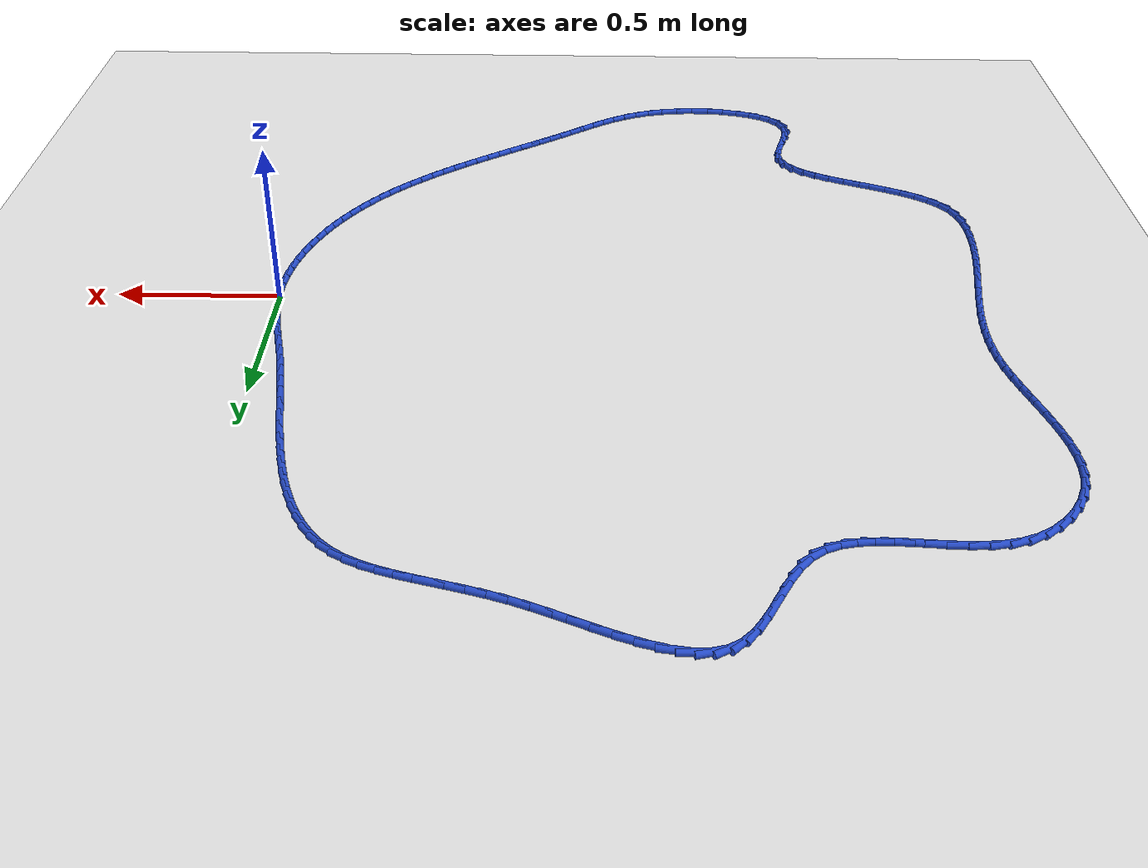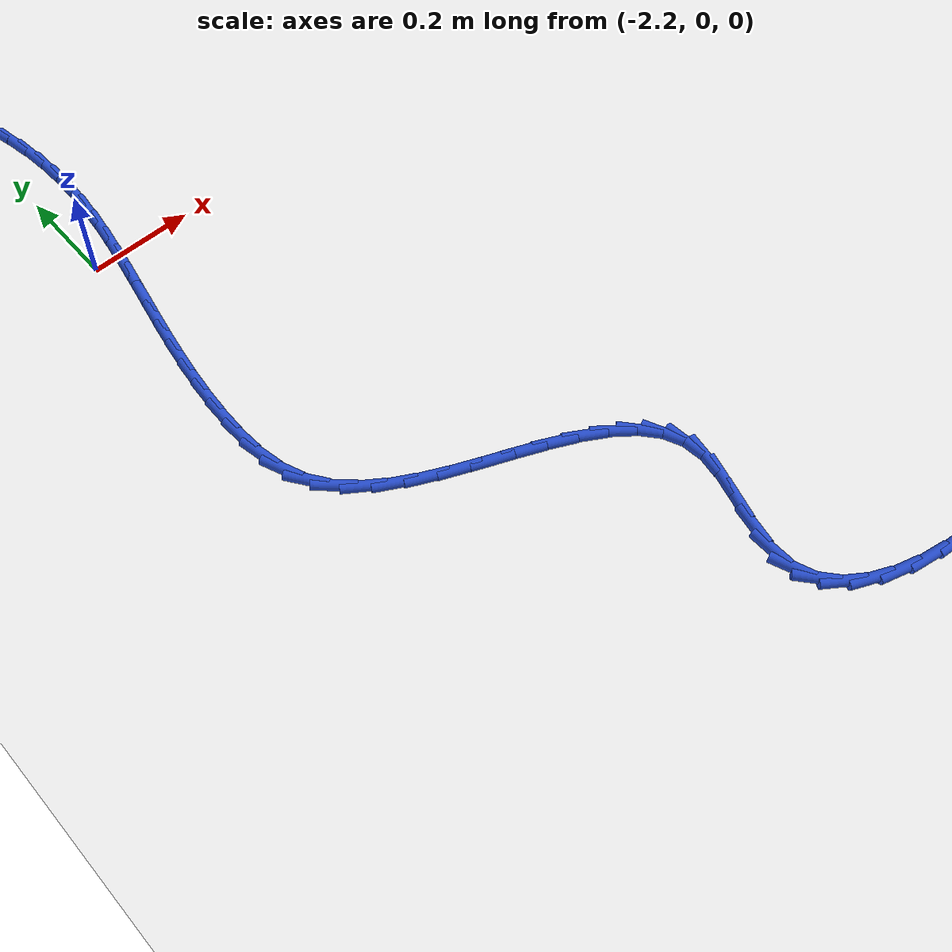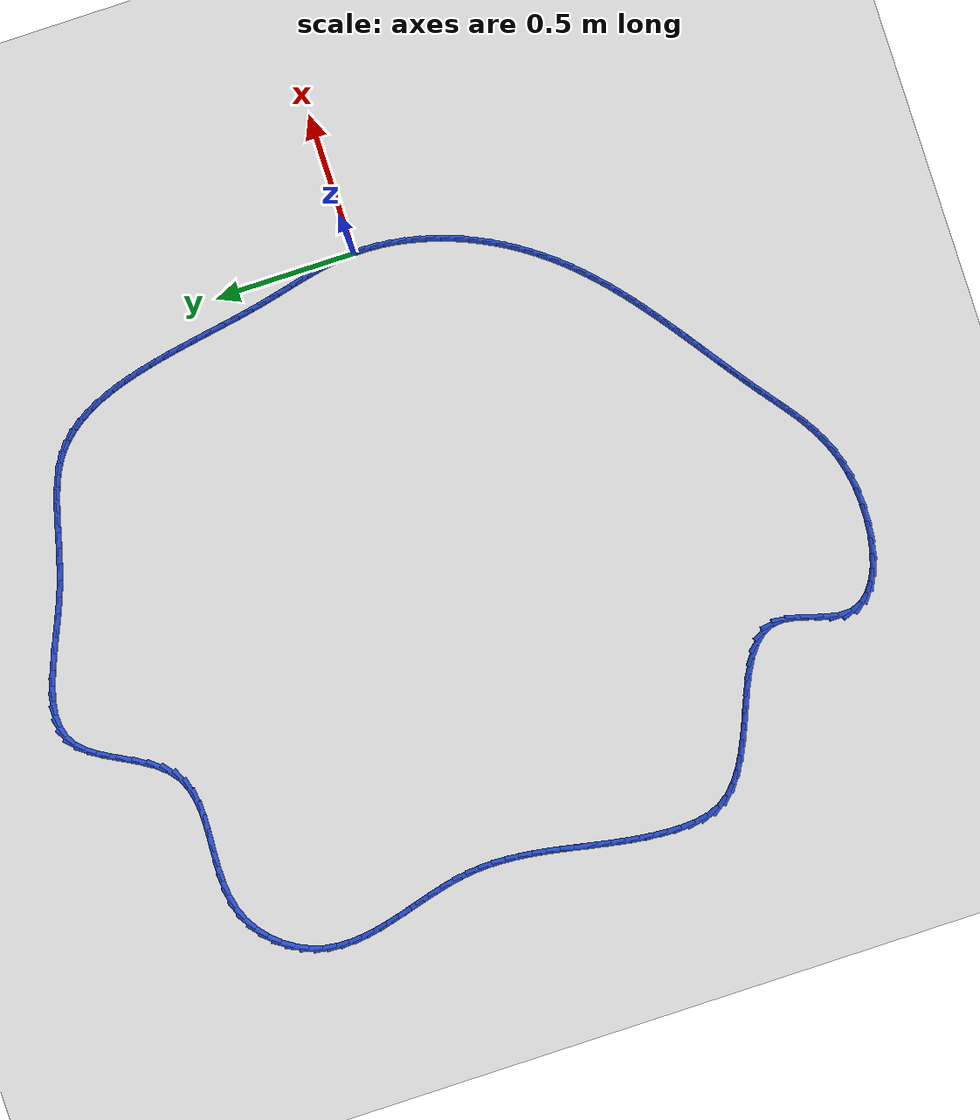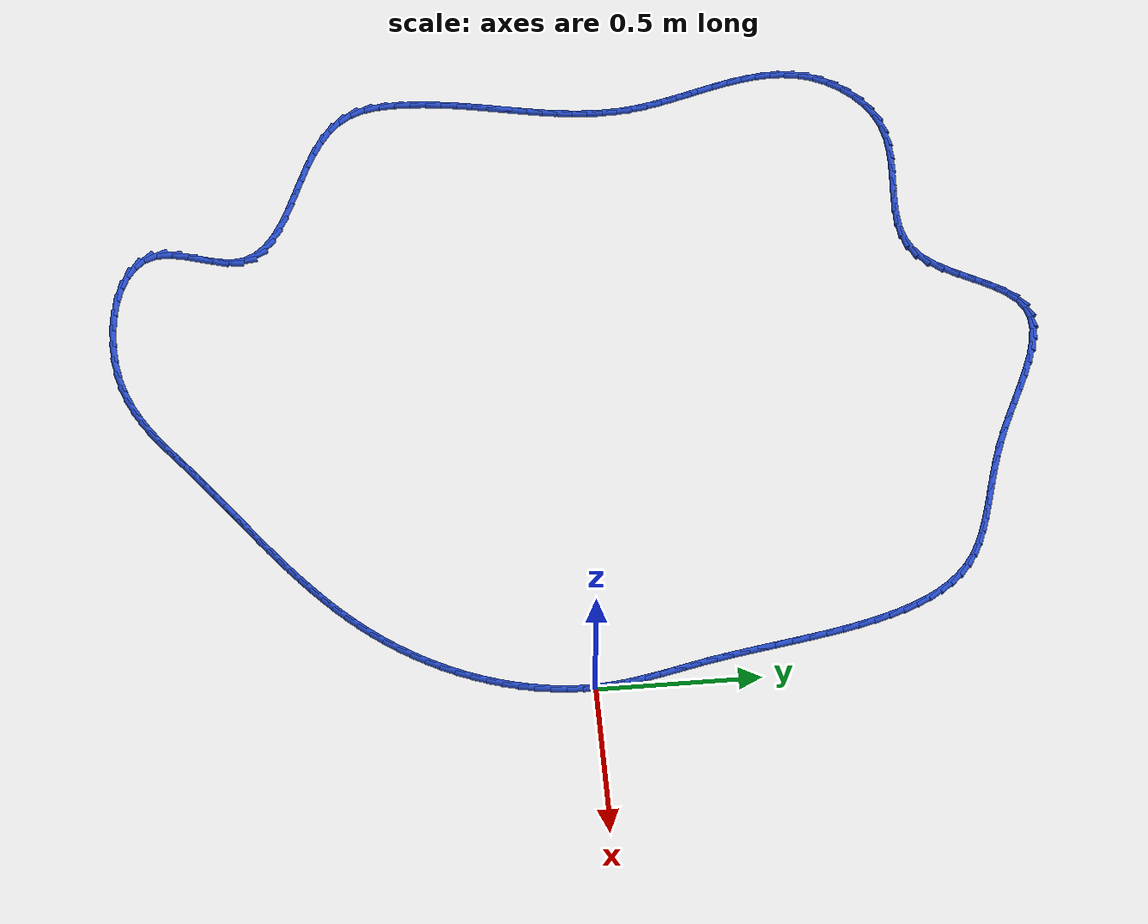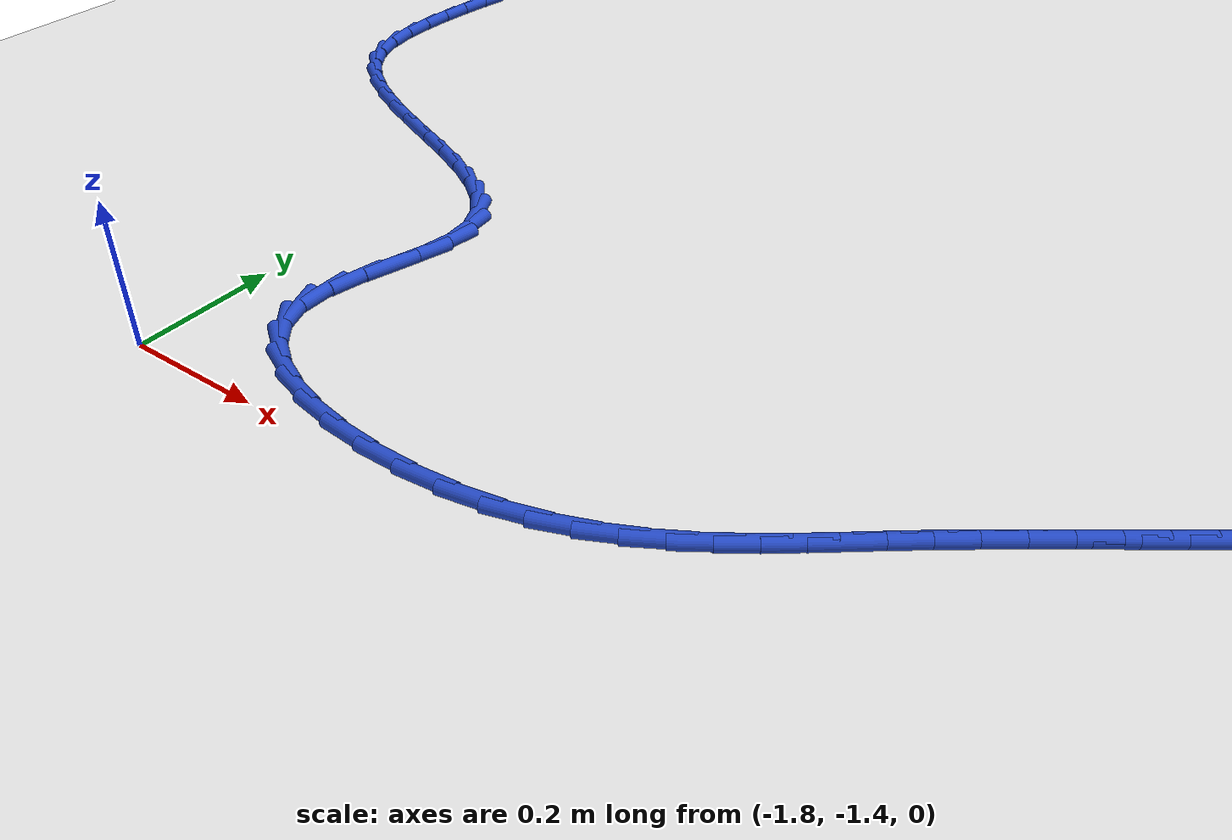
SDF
<sdf version="1.6">
 <world name="default">
  <light name="sun" type="directional">
   <pose>0 0 10 0 -0 0</pose>
   <diffuse>0.8 0.8 0.8 1</diffuse>
   <specular>0.2 0.2 0.2 1</specular>
   <attenuation>
    <range>1000</range>
    <constant>0.9</constant>
    <linear>0.01</linear>
    <quadratic>0.001</quadratic>
   </attenuation>
   <direction>-0.5 0.1 -0.9</direction>
  </light>
  <model name="ground_plane">
   <static>1</static>
   <link name="link">
    <collision name="collision">
     <geometry><plane><normal>0 0 1</normal><size>100 100</size></plane></geometry>
     <surface><friction><ode><mu>100</mu><mu2>50</mu2></ode></friction></surface>
    </collision>
    <visual name="visual">
     <cast_shadows>0</cast_shadows>
     <geometry><plane><normal>0 0 1</normal><size>100 100</size></plane></geometry>
     <material>
      <script><uri>file://media/materials/scripts/gazebo.material</uri><name>Gazebo/WhiteGlow</name></script>
     </material>
    </visual>
   </link>
  </model>
  <gravity>0 0 -9.8</gravity>
  <magnetic_field>6e-06 2.3e-05 -4.2e-05</magnetic_field>
  <atmosphere type="adiabatic"/>
  <physics name="default_physics" default="0" type="ode">
   <max_step_size>0.001</max_step_size>
   <real_time_factor>1</real_time_factor>
   <real_time_update_rate>1000</real_time_update_rate>
  </physics>
  <scene><ambient>0.4 0.4 0.4 1</ambient><background>0.7 0.7 0.7 1</background><shadows>1</shadows></scene>
  <spherical_coordinates>
   <surface_model>EARTH_WGS84</surface_model>
   <latitude_deg>0</latitude_deg>
   <longitude_deg>0</longitude_deg>
   <elevation>0</elevation>
   <heading_deg>0</heading_deg>
  </spherical_coordinates>
  <model name="line">
   <link name="link_0">
    <pose>2.949029909160572e-17 1.3877787807814457e-17 0.01 0 1.57 -1.4985770990119722</pose>
    <collision name="collision">
     <geometry><cylinder><radius>0.01</radius><length>0.08</length></cylinder></geometry>
    </collision>
    <visual name="visual">
     <material>
      <script><name>Gazebo/Blue</name><uri>file://media/materials/scripts/gazebo.material</uri></script>
     </material>
     <geometry><cylinder><radius>0.01</radius><length>0.08</length></cylinder></geometry>
    </visual>
   </link>
   <link name="link_1">
    <pose>-0.0033918439803330576 0.0468842603277983 0.01 0 1.57 -1.4418258776042745</pose>
    <collision name="collision">
     <geometry><cylinder><radius>0.01</radius><length>0.08</length></cylinder></geometry>
    </collision>
    <visual name="visual">
     <material>
      <script><name>Gazebo/Blue</name><uri>file://media/materials/scripts/gazebo.material</uri></script>
     </material>
     <geometry><cylinder><radius>0.01</radius><length>0.08</length></cylinder></geometry>
    </visual>
   </link>
   <link name="link_2">
    <pose>-0.009426393539881728 0.09341471846412026 0.01 0 1.57 -1.397143746763654</pose>
    <collision name="collision">
     <geometry><cylinder><radius>0.01</radius><length>0.08</length></cylinder></geometry>
    </collision>
    <visual name="visual">
     <material>
      <script><name>Gazebo/Blue</name><uri>file://media/materials/scripts/gazebo.material</uri></script>
     </material>
     <geometry><cylinder><radius>0.01</radius><length>0.08</length></cylinder></geometry>
    </visual>
   </link>
   <link name="link_3">
    <pose>-0.017572149075393492 0.13985060465585822 0.01 0 1.57 -1.3650510239960134</pose>
    <collision name="collision">
     <geometry><cylinder><radius>0.01</radius><length>0.08</length></cylinder></geometry>
    </collision>
    <visual name="visual">
     <material>
      <script><name>Gazebo/Blue</name><uri>file://media/materials/scripts/gazebo.material</uri></script>
     </material>
     <geometry><cylinder><radius>0.01</radius><length>0.08</length></cylinder></geometry>
    </visual>
   </link>
   <link name="link_4">
    <pose>-0.027297610983615894 0.18645114914990454 0.01 0 1.57 -1.3455753912851607</pose>
    <collision name="collision">
     <geometry><cylinder><radius>0.01</radius><length>0.08</length></cylinder></geometry>
    </collision>
    <visual name="visual">
     <material>
      <script><name>Gazebo/Blue</name><uri>file://media/materials/scripts/gazebo.material</uri></script>
     </material>
     <geometry><cylinder><radius>0.01</radius><length>0.08</length></cylinder></geometry>
    </visual>
   </link>
   <link name="link_5">
    <pose>-0.038071279661296434 0.23347558219315145 0.01 0 1.57 -1.338413678237085</pose>
    <collision name="collision">
     <geometry><cylinder><radius>0.01</radius><length>0.08</length></cylinder></geometry>
    </collision>
    <visual name="visual">
     <material>
      <script><name>Gazebo/Blue</name><uri>file://media/materials/scripts/gazebo.material</uri></script>
     </material>
     <geometry><cylinder><radius>0.01</radius><length>0.08</length></cylinder></geometry>
    </visual>
   </link>
   <link name="link_6">
    <pose>-0.049361655505182636 0.28118313403249134 0.01 0 1.57 -1.3430475991671973</pose>
    <collision name="collision">
     <geometry><cylinder><radius>0.01</radius><length>0.08</length></cylinder></geometry>
    </collision>
    <visual name="visual">
     <material>
      <script><name>Gazebo/Blue</name><uri>file://media/materials/scripts/gazebo.material</uri></script>
     </material>
     <geometry><cylinder><radius>0.01</radius><length>0.08</length></cylinder></geometry>
    </visual>
   </link>
   <link name="link_7">
    <pose>-0.06063723891202205 0.3298330349148165 0.01 0 1.57 -1.3586625292744745</pose>
    <collision name="collision">
     <geometry><cylinder><radius>0.01</radius><length>0.08</length></cylinder></geometry>
    </collision>
    <visual name="visual">
     <material>
      <script><name>Gazebo/Blue</name><uri>file://media/materials/scripts/gazebo.material</uri></script>
     </material>
     <geometry><cylinder><radius>0.01</radius><length>0.08</length></cylinder></geometry>
    </visual>
   </link>
   <link name="link_8">
    <pose>-0.07137293527979068 0.37967975036792156 0.01 0 1.57 -1.3778796878840285</pose>
    <collision name="collision">
     <geometry><cylinder><radius>0.01</radius><length>0.08</length></cylinder></geometry>
    </collision>
    <visual name="visual">
     <material>
      <script><name>Gazebo/Blue</name><uri>file://media/materials/scripts/gazebo.material</uri></script>
     </material>
     <geometry><cylinder><radius>0.01</radius><length>0.08</length></cylinder></geometry>
    </visual>
   </link>
   <link name="link_9">
    <pose>-0.08134936968535285 0.4307503192040393 0.01 0 1.57 -1.3913725739846556</pose>
    <collision name="collision">
     <geometry><cylinder><radius>0.01</radius><length>0.08</length></cylinder></geometry>
    </collision>
    <visual name="visual">
     <material>
      <script><name>Gazebo/Blue</name><uri>file://media/materials/scripts/gazebo.material</uri></script>
     </material>
     <geometry><cylinder><radius>0.01</radius><length>0.08</length></cylinder></geometry>
    </visual>
   </link>
   <link name="link_10">
    <pose>-0.09078064847961459 0.4827493108975732 0.01 0 1.57 -1.3988999933617758</pose>
    <collision name="collision">
     <geometry><cylinder><radius>0.01</radius><length>0.08</length></cylinder></geometry>
    </collision>
    <visual name="visual">
     <material>
      <script><name>Gazebo/Blue</name><uri>file://media/materials/scripts/gazebo.material</uri></script>
     </material>
     <geometry><cylinder><radius>0.01</radius><length>0.08</length></cylinder></geometry>
    </visual>
   </link>
   <link name="link_11">
    <pose>-0.09991381599921104 0.5353567921564089 0.01 0 1.57 -1.4007571224651425</pose>
    <collision name="collision">
     <geometry><cylinder><radius>0.01</radius><length>0.08</length></cylinder></geometry>
    </collision>
    <visual name="visual">
     <material>
      <script><name>Gazebo/Blue</name><uri>file://media/materials/scripts/gazebo.material</uri></script>
     </material>
     <geometry><cylinder><radius>0.01</radius><length>0.08</length></cylinder></geometry>
    </visual>
   </link>
   <link name="link_12">
    <pose>-0.10899591658077741 0.5882528296884322 0.01 0 1.57 -1.3970595021239554</pose>
    <collision name="collision">
     <geometry><cylinder><radius>0.01</radius><length>0.08</length></cylinder></geometry>
    </collision>
    <visual name="visual">
     <material>
      <script><name>Gazebo/Blue</name><uri>file://media/materials/scripts/gazebo.material</uri></script>
     </material>
     <geometry><cylinder><radius>0.01</radius><length>0.08</length></cylinder></geometry>
    </visual>
   </link>
   <link name="link_13">
    <pose>-0.11827399456094877 0.6411174902015286 0.01 0 1.57 -1.3877516949721467</pose>
    <collision name="collision">
     <geometry><cylinder><radius>0.01</radius><length>0.08</length></cylinder></geometry>
    </collision>
    <visual name="visual">
     <material>
      <script><name>Gazebo/Blue</name><uri>file://media/materials/scripts/gazebo.material</uri></script>
     </material>
     <geometry><cylinder><radius>0.01</radius><length>0.08</length></cylinder></geometry>
    </visual>
   </link>
   <link name="link_14">
    <pose>-0.12799509427636038 0.6936308404035842 0.01 0 1.57 -1.3726080922688408</pose>
    <collision name="collision">
     <geometry><cylinder><radius>0.01</radius><length>0.08</length></cylinder></geometry>
    </collision>
    <visual name="visual">
     <material>
      <script><name>Gazebo/Blue</name><uri>file://media/materials/scripts/gazebo.material</uri></script>
     </material>
     <geometry><cylinder><radius>0.01</radius><length>0.08</length></cylinder></geometry>
    </visual>
   </link>
   <link name="link_15">
    <pose>-0.13840626006364729 0.7454729470024842 0.01 0 1.57 -1.351226742205336</pose>
    <collision name="collision">
     <geometry><cylinder><radius>0.01</radius><length>0.08</length></cylinder></geometry>
    </collision>
    <visual name="visual">
     <material>
      <script><name>Gazebo/Blue</name><uri>file://media/materials/scripts/gazebo.material</uri></script>
     </material>
     <geometry><cylinder><radius>0.01</radius><length>0.08</length></cylinder></geometry>
    </visual>
   </link>
   <link name="link_16">
    <pose>-0.14975453625944482 0.7963238767061148 0.01 0 1.57 -1.3230178254168252</pose>
    <collision name="collision">
     <geometry><cylinder><radius>0.01</radius><length>0.08</length></cylinder></geometry>
    </collision>
    <visual name="visual">
     <material>
      <script><name>Gazebo/Blue</name><uri>file://media/materials/scripts/gazebo.material</uri></script>
     </material>
     <geometry><cylinder><radius>0.01</radius><length>0.08</length></cylinder></geometry>
    </visual>
   </link>
   <link name="link_17">
    <pose>-0.16228696720038802 0.8458636962223615 0.01 0 1.57 -1.287190034167568</pose>
    <collision name="collision">
     <geometry><cylinder><radius>0.01</radius><length>0.08</length></cylinder></geometry>
    </collision>
    <visual name="visual">
     <material>
      <script><name>Gazebo/Blue</name><uri>file://media/materials/scripts/gazebo.material</uri></script>
     </material>
     <geometry><cylinder><radius>0.01</radius><length>0.08</length></cylinder></geometry>
    </visual>
   </link>
   <link name="link_18">
    <pose>-0.17625059722311207 0.8937724722591098 0.01 0 1.57 -1.2427414599435607</pose>
    <collision name="collision">
     <geometry><cylinder><radius>0.01</radius><length>0.08</length></cylinder></geometry>
    </collision>
    <visual name="visual">
     <material>
      <script><name>Gazebo/Blue</name><uri>file://media/materials/scripts/gazebo.material</uri></script>
     </material>
     <geometry><cylinder><radius>0.01</radius><length>0.08</length></cylinder></geometry>
    </visual>
   </link>
   <link name="link_19">
    <pose>-0.19189247066425216 0.9397302715242458 0.01 0 1.57 -1.1884678519938565</pose>
    <collision name="collision">
     <geometry><cylinder><radius>0.01</radius><length>0.08</length></cylinder></geometry>
    </collision>
    <visual name="visual">
     <material>
      <script><name>Gazebo/Blue</name><uri>file://media/materials/scripts/gazebo.material</uri></script>
     </material>
     <geometry><cylinder><radius>0.01</radius><length>0.08</length></cylinder></geometry>
    </visual>
   </link>
   <link name="link_20">
    <pose>-0.20945963186044345 0.9834171607256552 0.01 0 1.57 -1.1230115500518927</pose>
    <collision name="collision">
     <geometry><cylinder><radius>0.01</radius><length>0.08</length></cylinder></geometry>
    </collision>
    <visual name="visual">
     <material>
      <script><name>Gazebo/Blue</name><uri>file://media/materials/scripts/gazebo.material</uri></script>
     </material>
     <geometry><cylinder><radius>0.01</radius><length>0.08</length></cylinder></geometry>
    </visual>
   </link>
   <link name="link_21">
    <pose>-0.22919912514832108 1.0245132065712232 0.01 0 1.57 -1.044988901586019</pose>
    <collision name="collision">
     <geometry><cylinder><radius>0.01</radius><length>0.08</length></cylinder></geometry>
    </collision>
    <visual name="visual">
     <material>
      <script><name>Gazebo/Blue</name><uri>file://media/materials/scripts/gazebo.material</uri></script>
     </material>
     <geometry><cylinder><radius>0.01</radius><length>0.08</length></cylinder></geometry>
    </visual>
   </link>
   <link name="link_22">
    <pose>-0.25135799486452015 1.062698475768836 0.01 0 1.57 -0.9532467809125815</pose>
    <collision name="collision">
     <geometry><cylinder><radius>0.01</radius><length>0.08</length></cylinder></geometry>
    </collision>
    <visual name="visual">
     <material>
      <script><name>Gazebo/Blue</name><uri>file://media/materials/scripts/gazebo.material</uri></script>
     </material>
     <geometry><cylinder><radius>0.01</radius><length>0.08</length></cylinder></geometry>
    </visual>
   </link>
   <link name="link_23">
    <pose>-0.27618328534567604 1.0976530350263796 0.01 0 1.57 -0.8472905187564059</pose>
    <collision name="collision">
     <geometry><cylinder><radius>0.01</radius><length>0.08</length></cylinder></geometry>
    </collision>
    <visual name="visual">
     <material>
      <script><name>Gazebo/Blue</name><uri>file://media/materials/scripts/gazebo.material</uri></script>
     </material>
     <geometry><cylinder><radius>0.01</radius><length>0.08</length></cylinder></geometry>
    </visual>
   </link>
   <link name="link_24">
    <pose>-0.30392204092842384 1.1290569510517394 0.01 0 1.57 -0.7278581985357417</pose>
    <collision name="collision">
     <geometry><cylinder><radius>0.01</radius><length>0.08</length></cylinder></geometry>
    </collision>
    <visual name="visual">
     <material>
      <script><name>Gazebo/Blue</name><uri>file://media/materials/scripts/gazebo.material</uri></script>
     </material>
     <geometry><cylinder><radius>0.01</radius><length>0.08</length></cylinder></geometry>
    </visual>
   </link>
   <link name="link_25">
    <pose>-0.3348213059493986 1.156590290552801 0.01 0 1.57 -0.599829708468835</pose>
    <collision name="collision">
     <geometry><cylinder><radius>0.01</radius><length>0.08</length></cylinder></geometry>
    </collision>
    <visual name="visual">
     <material>
      <script><name>Gazebo/Blue</name><uri>file://media/materials/scripts/gazebo.material</uri></script>
     </material>
     <geometry><cylinder><radius>0.01</radius><length>0.08</length></cylinder></geometry>
    </visual>
   </link>
   <link name="link_26">
    <pose>-0.3690835530213326 1.1800217905074926 0.01 0 1.57 -0.485533232569479</pose>
    <collision name="collision">
     <geometry><cylinder><radius>0.01</radius><length>0.08</length></cylinder></geometry>
    </collision>
    <visual name="visual">
     <material>
      <script><name>Gazebo/Blue</name><uri>file://media/materials/scripts/gazebo.material</uri></script>
     </material>
     <geometry><cylinder><radius>0.01</radius><length>0.08</length></cylinder></geometry>
    </visual>
   </link>
   <link name="link_27">
    <pose>-0.4065688197145622 1.1998014226547729 0.01 0 1.57 -0.39597505866669763</pose>
    <collision name="collision">
     <geometry><cylinder><radius>0.01</radius><length>0.08</length></cylinder></geometry>
    </collision>
    <visual name="visual">
     <material>
      <script><name>Gazebo/Blue</name><uri>file://media/materials/scripts/gazebo.material</uri></script>
     </material>
     <geometry><cylinder><radius>0.01</radius><length>0.08</length></cylinder></geometry>
    </visual>
   </link>
   <link name="link_28">
    <pose>-0.4469784152529325 1.2166949303509915 0.01 0 1.57 -0.33071761422270113</pose>
    <collision name="collision">
     <geometry><cylinder><radius>0.01</radius><length>0.08</length></cylinder></geometry>
    </collision>
    <visual name="visual">
     <material>
      <script><name>Gazebo/Blue</name><uri>file://media/materials/scripts/gazebo.material</uri></script>
     </material>
     <geometry><cylinder><radius>0.01</radius><length>0.08</length></cylinder></geometry>
    </visual>
   </link>
   <link name="link_29">
    <pose>-0.49001278054278613 1.2314697843693643 0.01 0 1.57 -0.2877270271286863</pose>
    <collision name="collision">
     <geometry><cylinder><radius>0.01</radius><length>0.08</length></cylinder></geometry>
    </collision>
    <visual name="visual">
     <material>
      <script><name>Gazebo/Blue</name><uri>file://media/materials/scripts/gazebo.material</uri></script>
     </material>
     <geometry><cylinder><radius>0.01</radius><length>0.08</length></cylinder></geometry>
    </visual>
   </link>
   <link name="link_30">
    <pose>-0.535372356490465 1.2448934554831037 0.01 0 1.57 -0.26461538843784094</pose>
    <collision name="collision">
     <geometry><cylinder><radius>0.01</radius><length>0.08</length></cylinder></geometry>
    </collision>
    <visual name="visual">
     <material>
      <script><name>Gazebo/Blue</name><uri>file://media/materials/scripts/gazebo.material</uri></script>
     </material>
     <geometry><cylinder><radius>0.01</radius><length>0.08</length></cylinder></geometry>
    </visual>
   </link>
   <link name="link_31">
    <pose>-0.5827575840023123 1.2577334144654242 0.01 0 1.57 -0.2592210990552404</pose>
    <collision name="collision">
     <geometry><cylinder><radius>0.01</radius><length>0.08</length></cylinder></geometry>
    </collision>
    <visual name="visual">
     <material>
      <script><name>Gazebo/Blue</name><uri>file://media/materials/scripts/gazebo.material</uri></script>
     </material>
     <geometry><cylinder><radius>0.01</radius><length>0.08</length></cylinder></geometry>
    </visual>
   </link>
   <link name="link_32">
    <pose>-0.6318689039846701 1.2707571320895397 0.01 0 1.57 -0.26978283371711775</pose>
    <collision name="collision">
     <geometry><cylinder><radius>0.01</radius><length>0.08</length></cylinder></geometry>
    </collision>
    <visual name="visual">
     <material>
      <script><name>Gazebo/Blue</name><uri>file://media/materials/scripts/gazebo.material</uri></script>
     </material>
     <geometry><cylinder><radius>0.01</radius><length>0.08</length></cylinder></geometry>
    </visual>
   </link>
   <link name="link_33">
    <pose>-0.6824067573438809 1.2847320791286636 0.01 0 1.57 -0.2949016783012847</pose>
    <collision name="collision">
     <geometry><cylinder><radius>0.01</radius><length>0.08</length></cylinder></geometry>
    </collision>
    <visual name="visual">
     <material>
      <script><name>Gazebo/Blue</name><uri>file://media/materials/scripts/gazebo.material</uri></script>
     </material>
     <geometry><cylinder><radius>0.01</radius><length>0.08</length></cylinder></geometry>
    </visual>
   </link>
   <link name="link_34">
    <pose>-0.7340715849862872 1.300425726356011 0.01 0 1.57 -0.3334043114264832</pose>
    <collision name="collision">
     <geometry><cylinder><radius>0.01</radius><length>0.08</length></cylinder></geometry>
    </collision>
    <visual name="visual">
     <material>
      <script><name>Gazebo/Blue</name><uri>file://media/materials/scripts/gazebo.material</uri></script>
     </material>
     <geometry><cylinder><radius>0.01</radius><length>0.08</length></cylinder></geometry>
    </visual>
   </link>
   <link name="link_35">
    <pose>-0.7865638263673819 1.318605523849465 0.01 0 1.57 -0.37798311117815814</pose>
    <collision name="collision">
     <geometry><cylinder><radius>0.01</radius><length>0.08</length></cylinder></geometry>
    </collision>
    <visual name="visual">
     <material>
      <script><name>Gazebo/Blue</name><uri>file://media/materials/scripts/gazebo.material</uri></script>
     </material>
     <geometry><cylinder><radius>0.01</radius><length>0.08</length></cylinder></geometry>
    </visual>
   </link>
   <link name="link_36">
    <pose>-0.8395564898213262 1.3396476363814371 0.01 0 1.57 -0.40718763113563555</pose>
    <collision name="collision">
     <geometry><cylinder><radius>0.01</radius><length>0.08</length></cylinder></geometry>
    </collision>
    <visual name="visual">
     <material>
      <script><name>Gazebo/Blue</name><uri>file://media/materials/scripts/gazebo.material</uri></script>
     </material>
     <geometry><cylinder><radius>0.01</radius><length>0.08</length></cylinder></geometry>
    </visual>
   </link>
   <link name="link_37">
    <pose>-0.8926249547335804 1.3625356216721456 0.01 0 1.57 -0.4180092884224215</pose>
    <collision name="collision">
     <geometry><cylinder><radius>0.01</radius><length>0.08</length></cylinder></geometry>
    </collision>
    <visual name="visual">
     <material>
      <script><name>Gazebo/Blue</name><uri>file://media/materials/scripts/gazebo.material</uri></script>
     </material>
     <geometry><cylinder><radius>0.01</radius><length>0.08</length></cylinder></geometry>
    </visual>
   </link>
   <link name="link_38">
    <pose>-0.9453228902887438 1.385943356970774 0.01 0 1.57 -0.41084642765536583</pose>
    <collision name="collision">
     <geometry><cylinder><radius>0.01</radius><length>0.08</length></cylinder></geometry>
    </collision>
    <visual name="visual">
     <material>
      <script><name>Gazebo/Blue</name><uri>file://media/materials/scripts/gazebo.material</uri></script>
     </material>
     <geometry><cylinder><radius>0.01</radius><length>0.08</length></cylinder></geometry>
    </visual>
   </link>
   <link name="link_39">
    <pose>-0.9972039656714178 1.4085447195265073 0.01 0 1.57 -0.3842766454186065</pose>
    <collision name="collision">
     <geometry><cylinder><radius>0.01</radius><length>0.08</length></cylinder></geometry>
    </collision>
    <visual name="visual">
     <material>
      <script><name>Gazebo/Blue</name><uri>file://media/materials/scripts/gazebo.material</uri></script>
     </material>
     <geometry><cylinder><radius>0.01</radius><length>0.08</length></cylinder></geometry>
    </visual>
   </link>
   <link name="link_40">
    <pose>-1.0478218500662029 1.4290135865885303 0.01 0 1.57 -0.334712112047795</pose>
    <collision name="collision">
     <geometry><cylinder><radius>0.01</radius><length>0.08</length></cylinder></geometry>
    </collision>
    <visual name="visual">
     <material>
      <script><name>Gazebo/Blue</name><uri>file://media/materials/scripts/gazebo.material</uri></script>
     </material>
     <geometry><cylinder><radius>0.01</radius><length>0.08</length></cylinder></geometry>
    </visual>
   </link>
   <link name="link_41">
    <pose>-1.0967302126576994 1.446023835406027 0.01 0 1.57 -0.255767088914733</pose>
    <collision name="collision">
     <geometry><cylinder><radius>0.01</radius><length>0.08</length></cylinder></geometry>
    </collision>
    <visual name="visual">
     <material>
      <script><name>Gazebo/Blue</name><uri>file://media/materials/scripts/gazebo.material</uri></script>
     </material>
     <geometry><cylinder><radius>0.01</radius><length>0.08</length></cylinder></geometry>
    </visual>
   </link>
   <link name="link_42">
    <pose>-1.1434827226305084 1.458249343228183 0.01 0 1.57 -0.13762055963404898</pose>
    <collision name="collision">
     <geometry><cylinder><radius>0.01</radius><length>0.08</length></cylinder></geometry>
    </collision>
    <visual name="visual">
     <material>
      <script><name>Gazebo/Blue</name><uri>file://media/materials/scripts/gazebo.material</uri></script>
     </material>
     <geometry><cylinder><radius>0.01</radius><length>0.08</length></cylinder></geometry>
    </visual>
   </link>
   <link name="link_43">
    <pose>-1.1876330491692293 1.4643639873041816 0.01 0 1.57 0.03216126967364137</pose>
    <collision name="collision">
     <geometry><cylinder><radius>0.01</radius><length>0.08</length></cylinder></geometry>
    </collision>
    <visual name="visual">
     <material>
      <script><name>Gazebo/Blue</name><uri>file://media/materials/scripts/gazebo.material</uri></script>
     </material>
     <geometry><cylinder><radius>0.01</radius><length>0.08</length></cylinder></geometry>
    </visual>
   </link>
   <link name="link_44">
    <pose>-1.2287348614584637 1.4630416448832073 0.01 0 1.57 0.26201509878968204</pose>
    <collision name="collision">
     <geometry><cylinder><radius>0.01</radius><length>0.08</length></cylinder></geometry>
    </collision>
    <visual name="visual">
     <material>
      <script><name>Gazebo/Blue</name><uri>file://media/materials/scripts/gazebo.material</uri></script>
     </material>
     <geometry><cylinder><radius>0.01</radius><length>0.08</length></cylinder></geometry>
    </visual>
   </link>
   <link name="link_45">
    <pose>-1.2663418286828123 1.4529561932144455 0.01 0 1.57 0.5398186192638539</pose>
    <collision name="collision">
     <geometry><cylinder><radius>0.01</radius><length>0.08</length></cylinder></geometry>
    </collision>
    <visual name="visual">
     <material>
      <script><name>Gazebo/Blue</name><uri>file://media/materials/scripts/gazebo.material</uri></script>
     </material>
     <geometry><cylinder><radius>0.01</radius><length>0.08</length></cylinder></geometry>
    </visual>
   </link>
   <link name="link_46">
    <pose>-1.3000085020764252 1.4327836916100332 0.01 0 1.57 0.7994982813043418</pose>
    <collision name="collision">
     <geometry><cylinder><radius>0.01</radius><length>0.08</length></cylinder></geometry>
    </collision>
    <visual name="visual">
     <material>
      <script><name>Gazebo/Blue</name><uri>file://media/materials/scripts/gazebo.material</uri></script>
     </material>
     <geometry><cylinder><radius>0.01</radius><length>0.08</length></cylinder></geometry>
    </visual>
   </link>
   <link name="link_47">
    <pose>-1.3297077006797173 1.4022349334101647 0.01 0 1.57 0.9632050527010525</pose>
    <collision name="collision">
     <geometry><cylinder><radius>0.01</radius><length>0.08</length></cylinder></geometry>
    </collision>
    <visual name="visual">
     <material>
      <script><name>Gazebo/Blue</name><uri>file://media/materials/scripts/gazebo.material</uri></script>
     </material>
     <geometry><cylinder><radius>0.01</radius><length>0.08</length></cylinder></geometry>
    </visual>
   </link>
   <link name="link_48">
    <pose>-1.3564979605696286 1.363706618796815 0.01 0 1.57 1.0490110748656216</pose>
    <collision name="collision">
     <geometry><cylinder><radius>0.01</radius><length>0.08</length></cylinder></geometry>
    </collision>
    <visual name="visual">
     <material>
      <script><name>Gazebo/Blue</name><uri>file://media/materials/scripts/gazebo.material</uri></script>
     </material>
     <geometry><cylinder><radius>0.01</radius><length>0.08</length></cylinder></geometry>
    </visual>
   </link>
   <link name="link_49">
    <pose>-1.3816116969503112 1.3200255997518338 0.01 0 1.57 1.0785972706311933</pose>
    <collision name="collision">
     <geometry><cylinder><radius>0.01</radius><length>0.08</length></cylinder></geometry>
    </collision>
    <visual name="visual">
     <material>
      <script><name>Gazebo/Blue</name><uri>file://media/materials/scripts/gazebo.material</uri></script>
     </material>
     <geometry><cylinder><radius>0.01</radius><length>0.08</length></cylinder></geometry>
    </visual>
   </link>
   <link name="link_50">
    <pose>-1.406281325025917 1.2740187282570699 0.01 0 1.57 1.0607322408314315</pose>
    <collision name="collision">
     <geometry><cylinder><radius>0.01</radius><length>0.08</length></cylinder></geometry>
    </collision>
    <visual name="visual">
     <material>
      <script><name>Gazebo/Blue</name><uri>file://media/materials/scripts/gazebo.material</uri></script>
     </material>
     <geometry><cylinder><radius>0.01</radius><length>0.08</length></cylinder></geometry>
    </visual>
   </link>
   <link name="link_51">
    <pose>-1.431739260000597 1.228512856294374 0.01 0 1.57 0.9933727275090164</pose>
    <collision name="collision">
     <geometry><cylinder><radius>0.01</radius><length>0.08</length></cylinder></geometry>
    </collision>
    <visual name="visual">
     <material>
      <script><name>Gazebo/Blue</name><uri>file://media/materials/scripts/gazebo.material</uri></script>
     </material>
     <geometry><cylinder><radius>0.01</radius><length>0.08</length></cylinder></geometry>
    </visual>
   </link>
   <link name="link_52">
    <pose>-1.4592179170785027 1.1863348358455943 0.01 0 1.57 0.8645004404029248</pose>
    <collision name="collision">
     <geometry><cylinder><radius>0.01</radius><length>0.08</length></cylinder></geometry>
    </collision>
    <visual name="visual">
     <material>
      <script><name>Gazebo/Blue</name><uri>file://media/materials/scripts/gazebo.material</uri></script>
     </material>
     <geometry><cylinder><radius>0.01</radius><length>0.08</length></cylinder></geometry>
    </visual>
   </link>
   <link name="link_53">
    <pose>-1.489949711463786 1.1503115188925819 0.01 0 1.57 0.657821341731498</pose>
    <collision name="collision">
     <geometry><cylinder><radius>0.01</radius><length>0.08</length></cylinder></geometry>
    </collision>
    <visual name="visual">
     <material>
      <script><name>Gazebo/Blue</name><uri>file://media/materials/scripts/gazebo.material</uri></script>
     </material>
     <geometry><cylinder><radius>0.01</radius><length>0.08</length></cylinder></geometry>
    </visual>
   </link>
   <link name="link_54">
    <pose>-1.5251125351433734 1.123144023288106 0.01 0 1.57 0.4234418613173065</pose>
    <collision name="collision">
     <geometry><cylinder><radius>0.01</radius><length>0.08</length></cylinder></geometry>
    </collision>
    <visual name="visual">
     <material>
      <script><name>Gazebo/Blue</name><uri>file://media/materials/scripts/gazebo.material</uri></script>
     </material>
     <geometry><cylinder><radius>0.01</radius><length>0.08</length></cylinder></geometry>
    </visual>
   </link>
   <link name="link_55">
    <pose>-1.5648810920524108 1.105220049181201 0.01 0 1.57 0.23216177421498163</pose>
    <collision name="collision">
     <geometry><cylinder><radius>0.01</radius><length>0.08</length></cylinder></geometry>
    </collision>
    <visual name="visual">
     <material>
      <script><name>Gazebo/Blue</name><uri>file://media/materials/scripts/gazebo.material</uri></script>
     </material>
     <geometry><cylinder><radius>0.01</radius><length>0.08</length></cylinder></geometry>
    </visual>
   </link>
   <link name="link_56">
    <pose>-1.6085491644997822 1.0948958334452192 0.01 0 1.57 0.09446770056954061</pose>
    <collision name="collision">
     <geometry><cylinder><radius>0.01</radius><length>0.08</length></cylinder></geometry>
    </collision>
    <visual name="visual">
     <material>
      <script><name>Gazebo/Blue</name><uri>file://media/materials/scripts/gazebo.material</uri></script>
     </material>
     <geometry><cylinder><radius>0.01</radius><length>0.08</length></cylinder></geometry>
    </visual>
   </link>
   <link name="link_57">
    <pose>-1.6553805944229403 1.0904585684855226 0.01 0 1.57 0.005341587435091712</pose>
    <collision name="collision">
     <geometry><cylinder><radius>0.01</radius><length>0.08</length></cylinder></geometry>
    </collision>
    <visual name="visual">
     <material>
      <script><name>Gazebo/Blue</name><uri>file://media/materials/scripts/gazebo.material</uri></script>
     </material>
     <geometry><cylinder><radius>0.01</radius><length>0.08</length></cylinder></geometry>
    </visual>
   </link>
   <link name="link_58">
    <pose>-1.7046392237593366 1.0901954467074724 0.01 0 1.57 -0.043118067844145326</pose>
    <collision name="collision">
     <geometry><cylinder><radius>0.01</radius><length>0.08</length></cylinder></geometry>
    </collision>
    <visual name="visual">
     <material>
      <script><name>Gazebo/Blue</name><uri>file://media/materials/scripts/gazebo.material</uri></script>
     </material>
     <geometry><cylinder><radius>0.01</radius><length>0.08</length></cylinder></geometry>
    </visual>
   </link>
   <link name="link_59">
    <pose>-1.7555888944464226 1.0923936605164308 0.01 0 1.57 -0.05671144065306227</pose>
    <collision name="collision">
     <geometry><cylinder><radius>0.01</radius><length>0.08</length></cylinder></geometry>
    </collision>
    <visual name="visual">
     <material>
      <script><name>Gazebo/Blue</name><uri>file://media/materials/scripts/gazebo.material</uri></script>
     </material>
     <geometry><cylinder><radius>0.01</radius><length>0.08</length></cylinder></geometry>
    </visual>
   </link>
   <link name="link_60">
    <pose>-1.807493448421651 1.0953404023177602 0.01 0 1.57 -0.038015779506397666</pose>
    <collision name="collision">
     <geometry><cylinder><radius>0.01</radius><length>0.08</length></cylinder></geometry>
    </collision>
    <visual name="visual">
     <material>
      <script><name>Gazebo/Blue</name><uri>file://media/materials/scripts/gazebo.material</uri></script>
     </material>
     <geometry><cylinder><radius>0.01</radius><length>0.08</length></cylinder></geometry>
    </visual>
   </link>
   <link name="link_61">
    <pose>-1.8596167276224738 1.0973228645168218 0.01 0 1.57 0.013459386897508295</pose>
    <collision name="collision">
     <geometry><cylinder><radius>0.01</radius><length>0.08</length></cylinder></geometry>
    </collision>
    <visual name="visual">
     <material>
      <script><name>Gazebo/Blue</name><uri>file://media/materials/scripts/gazebo.material</uri></script>
     </material>
     <geometry><cylinder><radius>0.01</radius><length>0.08</length></cylinder></geometry>
    </visual>
   </link>
   <link name="link_62">
    <pose>-1.911222573986342 1.096628239518978 0.01 0 1.57 0.10063785307828729</pose>
    <collision name="collision">
     <geometry><cylinder><radius>0.01</radius><length>0.08</length></cylinder></geometry>
    </collision>
    <visual name="visual">
     <material>
      <script><name>Gazebo/Blue</name><uri>file://media/materials/scripts/gazebo.material</uri></script>
     </material>
     <geometry><cylinder><radius>0.01</radius><length>0.08</length></cylinder></geometry>
    </visual>
   </link>
   <link name="link_63">
    <pose>-1.9615748294507087 1.0915437197295907 0.01 0 1.57 0.22732184701287741</pose>
    <collision name="collision">
     <geometry><cylinder><radius>0.01</radius><length>0.08</length></cylinder></geometry>
    </collision>
    <visual name="visual">
     <material>
      <script><name>Gazebo/Blue</name><uri>file://media/materials/scripts/gazebo.material</uri></script>
     </material>
     <geometry><cylinder><radius>0.01</radius><length>0.08</length></cylinder></geometry>
    </visual>
   </link>
   <link name="link_64">
    <pose>-2.009937335953025 1.0803564975540216 0.01 0 1.57 0.39228975317552417</pose>
    <collision name="collision">
     <geometry><cylinder><radius>0.01</radius><length>0.08</length></cylinder></geometry>
    </collision>
    <visual name="visual">
     <material>
      <script><name>Gazebo/Blue</name><uri>file://media/materials/scripts/gazebo.material</uri></script>
     </material>
     <geometry><cylinder><radius>0.01</radius><length>0.08</length></cylinder></geometry>
    </visual>
   </link>
   <link name="link_65">
    <pose>-2.0555713598951235 1.0614761463930935 0.01 0 1.57 0.5612290174973782</pose>
    <collision name="collision">
     <geometry><cylinder><radius>0.01</radius><length>0.08</length></cylinder></geometry>
    </collision>
    <visual name="visual">
     <material>
      <script><name>Gazebo/Blue</name><uri>file://media/materials/scripts/gazebo.material</uri></script>
     </material>
     <geometry><cylinder><radius>0.01</radius><length>0.08</length></cylinder></geometry>
    </visual>
   </link>
   <link name="link_66">
    <pose>-2.097702866647926 1.0349896287199445 0.01 0 1.57 0.7141424548129879</pose>
    <collision name="collision">
     <geometry><cylinder><radius>0.01</radius><length>0.08</length></cylinder></geometry>
    </collision>
    <visual name="visual">
     <material>
      <script><name>Gazebo/Blue</name><uri>file://media/materials/scripts/gazebo.material</uri></script>
     </material>
     <geometry><cylinder><radius>0.01</radius><length>0.08</length></cylinder></geometry>
    </visual>
   </link>
   <link name="link_67">
    <pose>-2.1355322124897413 1.0022007669971567 0.01 0 1.57 0.8566821413677169</pose>
    <collision name="collision">
     <geometry><cylinder><radius>0.01</radius><length>0.08</length></cylinder></geometry>
    </collision>
    <visual name="visual">
     <material>
      <script><name>Gazebo/Blue</name><uri>file://media/materials/scripts/gazebo.material</uri></script>
     </material>
     <geometry><cylinder><radius>0.01</radius><length>0.08</length></cylinder></geometry>
    </visual>
   </link>
   <link name="link_68">
    <pose>-2.1682591793660575 0.9644406740970677 0.01 0 1.57 0.9958788411107538</pose>
    <collision name="collision">
     <geometry><cylinder><radius>0.01</radius><length>0.08</length></cylinder></geometry>
    </collision>
    <visual name="visual">
     <material>
      <script><name>Gazebo/Blue</name><uri>file://media/materials/scripts/gazebo.material</uri></script>
     </material>
     <geometry><cylinder><radius>0.01</radius><length>0.08</length></cylinder></geometry>
    </visual>
   </link>
   <link name="link_69">
    <pose>-2.1950835492223617 0.9230404628920175 0.01 0 1.57 1.1393683113650093</pose>
    <collision name="collision">
     <geometry><cylinder><radius>0.01</radius><length>0.08</length></cylinder></geometry>
    </collision>
    <visual name="visual">
     <material>
      <script><name>Gazebo/Blue</name><uri>file://media/materials/scripts/gazebo.material</uri></script>
     </material>
     <geometry><cylinder><radius>0.01</radius><length>0.08</length></cylinder></geometry>
    </visual>
   </link>
   <link name="link_70">
    <pose>-2.215205113431188 0.8793312395615878 0.01 0 1.57 1.2904233244219105</pose>
    <collision name="collision">
     <geometry><cylinder><radius>0.01</radius><length>0.08</length></cylinder></geometry>
    </collision>
    <visual name="visual">
     <material>
      <script><name>Gazebo/Blue</name><uri>file://media/materials/scripts/gazebo.material</uri></script>
     </material>
     <geometry><cylinder><radius>0.01</radius><length>0.08</length></cylinder></geometry>
    </visual>
   </link>
   <link name="link_71">
    <pose>-2.2281372474664867 0.8344214804271715 0.01 0 1.57 1.4320874877064045</pose>
    <collision name="collision">
     <geometry><cylinder><radius>0.01</radius><length>0.08</length></cylinder></geometry>
    </collision>
    <visual name="visual">
     <material>
      <script><name>Gazebo/Blue</name><uri>file://media/materials/scripts/gazebo.material</uri></script>
     </material>
     <geometry><cylinder><radius>0.01</radius><length>0.08</length></cylinder></geometry>
    </visual>
   </link>
   <link name="link_72">
    <pose>-2.2345326646762285 0.7886107858876283 0.01 0 1.57 1.554270748800596</pose>
    <collision name="collision">
     <geometry><cylinder><radius>0.01</radius><length>0.08</length></cylinder></geometry>
    </collision>
    <visual name="visual">
     <material>
      <script><name>Gazebo/Blue</name><uri>file://media/materials/scripts/gazebo.material</uri></script>
     </material>
     <geometry><cylinder><radius>0.01</radius><length>0.08</length></cylinder></geometry>
    </visual>
   </link>
   <link name="link_73">
    <pose>-2.2353027552890388 0.7420151080095314 0.01 0 1.57 -1.4875475170289387</pose>
    <collision name="collision">
     <geometry><cylinder><radius>0.01</radius><length>0.08</length></cylinder></geometry>
    </collision>
    <visual name="visual">
     <material>
      <script><name>Gazebo/Blue</name><uri>file://media/materials/scripts/gazebo.material</uri></script>
     </material>
     <geometry><cylinder><radius>0.01</radius><length>0.08</length></cylinder></geometry>
    </visual>
   </link>
   <link name="link_74">
    <pose>-2.231358909533541 0.6947503988594538 0.01 0 1.57 -1.410193427646849</pose>
    <collision name="collision">
     <geometry><cylinder><radius>0.01</radius><length>0.08</length></cylinder></geometry>
    </collision>
    <visual name="visual">
     <material>
      <script><name>Gazebo/Blue</name><uri>file://media/materials/scripts/gazebo.material</uri></script>
     </material>
     <geometry><cylinder><radius>0.01</radius><length>0.08</length></cylinder></geometry>
    </visual>
   </link>
   <link name="link_75">
    <pose>-2.2236125176383594 0.6469326105039694 0.01 0 1.57 -1.3538217442908465</pose>
    <collision name="collision">
     <geometry><cylinder><radius>0.01</radius><length>0.08</length></cylinder></geometry>
    </collision>
    <visual name="visual">
     <material>
      <script><name>Gazebo/Blue</name><uri>file://media/materials/scripts/gazebo.material</uri></script>
     </material>
     <geometry><cylinder><radius>0.01</radius><length>0.08</length></cylinder></geometry>
    </visual>
   </link>
   <link name="link_76">
    <pose>-2.2129749698321164 0.5986776950096513 0.01 0 1.57 -1.316668740241282</pose>
    <collision name="collision">
     <geometry><cylinder><radius>0.01</radius><length>0.08</length></cylinder></geometry>
    </collision>
    <visual name="visual">
     <material>
      <script><name>Gazebo/Blue</name><uri>file://media/materials/scripts/gazebo.material</uri></script>
     </material>
     <geometry><cylinder><radius>0.01</radius><length>0.08</length></cylinder></geometry>
    </visual>
   </link>
   <link name="link_77">
    <pose>-2.2003576563434373 0.5501016044430723 0.01 0 1.57 -1.2972759444066857</pose>
    <collision name="collision">
     <geometry><cylinder><radius>0.01</radius><length>0.08</length></cylinder></geometry>
    </collision>
    <visual name="visual">
     <material>
      <script><name>Gazebo/Blue</name><uri>file://media/materials/scripts/gazebo.material</uri></script>
     </material>
     <geometry><cylinder><radius>0.01</radius><length>0.08</length></cylinder></geometry>
    </visual>
   </link>
   <link name="link_78">
    <pose>-2.186671967400946 0.5013202908708065 0.01 0 1.57 -1.2947749134154225</pose>
    <collision name="collision">
     <geometry><cylinder><radius>0.01</radius><length>0.08</length></cylinder></geometry>
    </collision>
    <visual name="visual">
     <material>
      <script><name>Gazebo/Blue</name><uri>file://media/materials/scripts/gazebo.material</uri></script>
     </material>
     <geometry><cylinder><radius>0.01</radius><length>0.08</length></cylinder></geometry>
    </visual>
   </link>
   <link name="link_79">
    <pose>-2.1728292932332645 0.4524497063594265 0.01 0 1.57 -1.3089857701829382</pose>
    <collision name="collision">
     <geometry><cylinder><radius>0.01</radius><length>0.08</length></cylinder></geometry>
    </collision>
    <visual name="visual">
     <material>
      <script><name>Gazebo/Blue</name><uri>file://media/materials/scripts/gazebo.material</uri></script>
     </material>
     <geometry><cylinder><radius>0.01</radius><length>0.08</length></cylinder></geometry>
    </visual>
   </link>
   <link name="link_80">
    <pose>-2.159741024069018 0.4036058029755064 0.01 0 1.57 -1.3404188184969796</pose>
    <collision name="collision">
     <geometry><cylinder><radius>0.01</radius><length>0.08</length></cylinder></geometry>
    </collision>
    <visual name="visual">
     <material>
      <script><name>Gazebo/Blue</name><uri>file://media/materials/scripts/gazebo.material</uri></script>
     </material>
     <geometry><cylinder><radius>0.01</radius><length>0.08</length></cylinder></geometry>
    </visual>
   </link>
   <link name="link_81">
    <pose>-2.1483185501368296 0.3549045327856191 0.01 0 1.57 -1.3901930392094646</pose>
    <collision name="collision">
     <geometry><cylinder><radius>0.01</radius><length>0.08</length></cylinder></geometry>
    </collision>
    <visual name="visual">
     <material>
      <script><name>Gazebo/Blue</name><uri>file://media/materials/scripts/gazebo.material</uri></script>
     </material>
     <geometry><cylinder><radius>0.01</radius><length>0.08</length></cylinder></geometry>
    </visual>
   </link>
   <link name="link_82">
    <pose>-2.1394732616653243 0.30646184785633757 0.01 0 1.57 -1.4570507985117958</pose>
    <collision name="collision">
     <geometry><cylinder><radius>0.01</radius><length>0.08</length></cylinder></geometry>
    </collision>
    <visual name="visual">
     <material>
      <script><name>Gazebo/Blue</name><uri>file://media/materials/scripts/gazebo.material</uri></script>
     </material>
     <geometry><cylinder><radius>0.01</radius><length>0.08</length></cylinder></geometry>
    </visual>
   </link>
   <link name="link_83">
    <pose>-2.13397983704595 0.25837457049239226 0.01 0 1.57 -1.5243254817757086</pose>
    <collision name="collision">
     <geometry><cylinder><radius>0.01</radius><length>0.08</length></cylinder></geometry>
    </collision>
    <visual name="visual">
     <material>
      <script><name>Gazebo/Blue</name><uri>file://media/materials/scripts/gazebo.material</uri></script>
     </material>
     <geometry><cylinder><radius>0.01</radius><length>0.08</length></cylinder></geometry>
    </visual>
   </link>
   <link name="link_84">
    <pose>-2.131759044680205 0.21062003740691143 0.01 0 1.57 1.5572460743168335</pose>
    <collision name="collision">
     <geometry><cylinder><radius>0.01</radius><length>0.08</length></cylinder></geometry>
    </collision>
    <visual name="visual">
     <material>
      <script><name>Gazebo/Blue</name><uri>file://media/materials/scripts/gazebo.material</uri></script>
     </material>
     <geometry><cylinder><radius>0.01</radius><length>0.08</length></cylinder></geometry>
    </visual>
   </link>
   <link name="link_85">
    <pose>-2.132402592289365 0.16312954063558616 0.01 0 1.57 1.5053674358403473</pose>
    <collision name="collision">
     <geometry><cylinder><radius>0.01</radius><length>0.08</length></cylinder></geometry>
    </collision>
    <visual name="visual">
     <material>
      <script><name>Gazebo/Blue</name><uri>file://media/materials/scripts/gazebo.material</uri></script>
     </material>
     <geometry><cylinder><radius>0.01</radius><length>0.08</length></cylinder></geometry>
    </visual>
   </link>
   <link name="link_86">
    <pose>-2.1355014924021956 0.11583427493747384 0.01 0 1.57 1.4621440461145194</pose>
    <collision name="collision">
     <geometry><cylinder><radius>0.01</radius><length>0.08</length></cylinder></geometry>
    </collision>
    <visual name="visual">
     <material>
      <script><name>Gazebo/Blue</name><uri>file://media/materials/scripts/gazebo.material</uri></script>
     </material>
     <geometry><cylinder><radius>0.01</radius><length>0.08</length></cylinder></geometry>
    </visual>
   </link>
   <link name="link_87">
    <pose>-2.1406467575474624 0.06866543507163242 0.01 0 1.57 1.427808000976461</pose>
    <collision name="collision">
     <geometry><cylinder><radius>0.01</radius><length>0.08</length></cylinder></geometry>
    </collision>
    <visual name="visual">
     <material>
      <script><name>Gazebo/Blue</name><uri>file://media/materials/scripts/gazebo.material</uri></script>
     </material>
     <geometry><cylinder><radius>0.01</radius><length>0.08</length></cylinder></geometry>
    </visual>
   </link>
   <link name="link_88">
    <pose>-2.147429400253933 0.021554215797119827 0.01 0 1.57 1.4024015469255213</pose>
    <collision name="collision">
     <geometry><cylinder><radius>0.01</radius><length>0.08</length></cylinder></geometry>
    </collision>
    <visual name="visual">
     <material>
      <script><name>Gazebo/Blue</name><uri>file://media/materials/scripts/gazebo.material</uri></script>
     </material>
     <geometry><cylinder><radius>0.01</radius><length>0.08</length></cylinder></geometry>
    </visual>
   </link>
   <link name="link_89">
    <pose>-2.1554404330503725 -0.02556818812700694 0.01 0 1.57 1.3858580002551069</pose>
    <collision name="collision">
     <geometry><cylinder><radius>0.01</radius><length>0.08</length></cylinder></geometry>
    </collision>
    <visual name="visual">
     <material>
      <script><name>Gazebo/Blue</name><uri>file://media/materials/scripts/gazebo.material</uri></script>
     </material>
     <geometry><cylinder><radius>0.01</radius><length>0.08</length></cylinder></geometry>
    </visual>
   </link>
   <link name="link_90">
    <pose>-2.1642708684655485 -0.07277058194168816 0.01 0 1.57 1.3780631359032487</pose>
    <collision name="collision">
     <geometry><cylinder><radius>0.01</radius><length>0.08</length></cylinder></geometry>
    </collision>
    <visual name="visual">
     <material>
      <script><name>Gazebo/Blue</name><uri>file://media/materials/scripts/gazebo.material</uri></script>
     </material>
     <geometry><cylinder><radius>0.01</radius><length>0.08</length></cylinder></geometry>
    </visual>
   </link>
   <link name="link_91">
    <pose>-2.173511719028226 -0.1201217708878668 0.01 0 1.57 1.378894332884143</pose>
    <collision name="collision">
     <geometry><cylinder><radius>0.01</radius><length>0.08</length></cylinder></geometry>
    </collision>
    <visual name="visual">
     <material>
      <script><name>Gazebo/Blue</name><uri>file://media/materials/scripts/gazebo.material</uri></script>
     </material>
     <geometry><cylinder><radius>0.01</radius><length>0.08</length></cylinder></geometry>
    </visual>
   </link>
   <link name="link_92">
    <pose>-2.1827539972671723 -0.16769056020648498 0.01 0 1.57 1.3882382271669589</pose>
    <collision name="collision">
     <geometry><cylinder><radius>0.01</radius><length>0.08</length></cylinder></geometry>
    </collision>
    <visual name="visual">
     <material>
      <script><name>Gazebo/Blue</name><uri>file://media/materials/scripts/gazebo.material</uri></script>
     </material>
     <geometry><cylinder><radius>0.01</radius><length>0.08</length></cylinder></geometry>
    </visual>
   </link>
   <link name="link_93">
    <pose>-2.191588715711154 -0.21554575513848478 0.01 0 1.57 1.4059886696610542</pose>
    <collision name="collision">
     <geometry><cylinder><radius>0.01</radius><length>0.08</length></cylinder></geometry>
    </collision>
    <visual name="visual">
     <material>
      <script><name>Gazebo/Blue</name><uri>file://media/materials/scripts/gazebo.material</uri></script>
     </material>
     <geometry><cylinder><radius>0.01</radius><length>0.08</length></cylinder></geometry>
    </visual>
   </link>
   <link name="link_94">
    <pose>-2.1996068868889376 -0.2637561609248092 0.01 0 1.57 1.432026743987751</pose>
    <collision name="collision">
     <geometry><cylinder><radius>0.01</radius><length>0.08</length></cylinder></geometry>
    </collision>
    <visual name="visual">
     <material>
      <script><name>Gazebo/Blue</name><uri>file://media/materials/scripts/gazebo.material</uri></script>
     </material>
     <geometry><cylinder><radius>0.01</radius><length>0.08</length></cylinder></geometry>
    </visual>
   </link>
   <link name="link_95">
    <pose>-2.2063995233292886 -0.3123905828063984 0.01 0 1.57 1.4661846281297624</pose>
    <collision name="collision">
     <geometry><cylinder><radius>0.01</radius><length>0.08</length></cylinder></geometry>
    </collision>
    <visual name="visual">
     <material>
      <script><name>Gazebo/Blue</name><uri>file://media/materials/scripts/gazebo.material</uri></script>
     </material>
     <geometry><cylinder><radius>0.01</radius><length>0.08</length></cylinder></geometry>
    </visual>
   </link>
   <link name="link_96">
    <pose>-2.211557637560974 -0.3615178260241955 0.01 0 1.57 1.5081960904036027</pose>
    <collision name="collision">
     <geometry><cylinder><radius>0.01</radius><length>0.08</length></cylinder></geometry>
    </collision>
    <visual name="visual">
     <material>
      <script><name>Gazebo/Blue</name><uri>file://media/materials/scripts/gazebo.material</uri></script>
     </material>
     <geometry><cylinder><radius>0.01</radius><length>0.08</length></cylinder></geometry>
    </visual>
   </link>
   <link name="link_97">
    <pose>-2.21467224211276 -0.4112066958191426 0.01 0 1.57 1.55995518831306</pose>
    <collision name="collision">
     <geometry><cylinder><radius>0.01</radius><length>0.08</length></cylinder></geometry>
    </collision>
    <visual name="visual">
     <material>
      <script><name>Gazebo/Blue</name><uri>file://media/materials/scripts/gazebo.material</uri></script>
     </material>
     <geometry><cylinder><radius>0.01</radius><length>0.08</length></cylinder></geometry>
    </visual>
   </link>
   <link name="link_98">
    <pose>-2.2152164239002996 -0.4614007293152093 0.01 0 1.57 -1.4990824895099022</pose>
    <collision name="collision">
     <geometry><cylinder><radius>0.01</radius><length>0.08</length></cylinder></geometry>
    </collision>
    <visual name="visual">
     <material>
      <script><name>Gazebo/Blue</name><uri>file://media/materials/scripts/gazebo.material</uri></script>
     </material>
     <geometry><cylinder><radius>0.01</radius><length>0.08</length></cylinder></geometry>
    </visual>
   </link>
   <link name="link_99">
    <pose>-2.21165531707378 -0.510972751841067 0.01 0 1.57 -1.3681878919831894</pose>
    <collision name="collision">
     <geometry><cylinder><radius>0.01</radius><length>0.08</length></cylinder></geometry>
    </collision>
    <visual name="visual">
     <material>
      <script><name>Gazebo/Blue</name><uri>file://media/materials/scripts/gazebo.material</uri></script>
     </material>
     <geometry><cylinder><radius>0.01</radius><length>0.08</length></cylinder></geometry>
    </visual>
   </link>
   <link name="link_100">
    <pose>-2.201942779980508 -0.5582524789175176 0.01 0 1.57 -1.1786231329613182</pose>
    <collision name="collision">
     <geometry><cylinder><radius>0.01</radius><length>0.08</length></cylinder></geometry>
    </collision>
    <visual name="visual">
     <material>
      <script><name>Gazebo/Blue</name><uri>file://media/materials/scripts/gazebo.material</uri></script>
     </material>
     <geometry><cylinder><radius>0.01</radius><length>0.08</length></cylinder></geometry>
    </visual>
   </link>
   <link name="link_101">
    <pose>-2.1840286703814376 -0.6015653763861077 0.01 0 1.57 -0.9448952439044634</pose>
    <collision name="collision">
     <geometry><cylinder><radius>0.01</radius><length>0.08</length></cylinder></geometry>
    </collision>
    <visual name="visual">
     <material>
      <script><name>Gazebo/Blue</name><uri>file://media/materials/scripts/gazebo.material</uri></script>
     </material>
     <geometry><cylinder><radius>0.01</radius><length>0.08</length></cylinder></geometry>
    </visual>
   </link>
   <link name="link_102">
    <pose>-2.1564937829238207 -0.6396572063404855 0.01 0 1.57 -0.7454336015631579</pose>
    <collision name="collision">
     <geometry><cylinder><radius>0.01</radius><length>0.08</length></cylinder></geometry>
    </collision>
    <visual name="visual">
     <material>
      <script><name>Gazebo/Blue</name><uri>file://media/materials/scripts/gazebo.material</uri></script>
     </material>
     <geometry><cylinder><radius>0.01</radius><length>0.08</length></cylinder></geometry>
    </visual>
   </link>
   <link name="link_103">
    <pose>-2.1204308261702276 -0.6729470329543393 0.01 0 1.57 -0.5998738383271485</pose>
    <collision name="collision">
     <geometry><cylinder><radius>0.01</radius><length>0.08</length></cylinder></geometry>
    </collision>
    <visual name="visual">
     <material>
      <script><name>Gazebo/Blue</name><uri>file://media/materials/scripts/gazebo.material</uri></script>
     </material>
     <geometry><cylinder><radius>0.01</radius><length>0.08</length></cylinder></geometry>
    </visual>
   </link>
   <link name="link_104">
    <pose>-2.077557542613134 -0.7022702844210893 0.01 0 1.57 -0.499811022221086</pose>
    <collision name="collision">
     <geometry><cylinder><radius>0.01</radius><length>0.08</length></cylinder></geometry>
    </collision>
    <visual name="visual">
     <material>
      <script><name>Gazebo/Blue</name><uri>file://media/materials/scripts/gazebo.material</uri></script>
     </material>
     <geometry><cylinder><radius>0.01</radius><length>0.08</length></cylinder></geometry>
    </visual>
   </link>
   <link name="link_105">
    <pose>-2.029591674745016 -0.7284623889341535 0.01 0 1.57 -0.4356252440007062</pose>
    <collision name="collision">
     <geometry><cylinder><radius>0.01</radius><length>0.08</length></cylinder></geometry>
    </collision>
    <visual name="visual">
     <material>
      <script><name>Gazebo/Blue</name><uri>file://media/materials/scripts/gazebo.material</uri></script>
     </material>
     <geometry><cylinder><radius>0.01</radius><length>0.08</length></cylinder></geometry>
    </visual>
   </link>
   <link name="link_106">
    <pose>-1.9782509650583453 -0.7523587746869526 0.01 0 1.57 -0.40046381622891153</pose>
    <collision name="collision">
     <geometry><cylinder><radius>0.01</radius><length>0.08</length></cylinder></geometry>
    </collision>
    <visual name="visual">
     <material>
      <script><name>Gazebo/Blue</name><uri>file://media/materials/scripts/gazebo.material</uri></script>
     </material>
     <geometry><cylinder><radius>0.01</radius><length>0.08</length></cylinder></geometry>
    </visual>
   </link>
   <link name="link_107">
    <pose>-1.9252531560455985 -0.7747948698729055 0.01 0 1.57 -0.3908263051395903</pose>
    <collision name="collision">
     <geometry><cylinder><radius>0.01</radius><length>0.08</length></cylinder></geometry>
    </collision>
    <visual name="visual">
     <material>
      <script><name>Gazebo/Blue</name><uri>file://media/materials/scripts/gazebo.material</uri></script>
     </material>
     <geometry><cylinder><radius>0.01</radius><length>0.08</length></cylinder></geometry>
    </visual>
   </link>
   <link name="link_108">
    <pose>-1.8723159901992508 -0.7966061026854325 0.01 0 1.57 -0.4064860488686914</pose>
    <collision name="collision">
     <geometry><cylinder><radius>0.01</radius><length>0.08</length></cylinder></geometry>
    </collision>
    <visual name="visual">
     <material>
      <script><name>Gazebo/Blue</name><uri>file://media/materials/scripts/gazebo.material</uri></script>
     </material>
     <geometry><cylinder><radius>0.01</radius><length>0.08</length></cylinder></geometry>
    </visual>
   </link>
   <link name="link_109">
    <pose>-1.8211572100117754 -0.818627901317953 0.01 0 1.57 -0.45075004899690807</pose>
    <collision name="collision">
     <geometry><cylinder><radius>0.01</radius><length>0.08</length></cylinder></geometry>
    </collision>
    <visual name="visual">
     <material>
      <script><name>Gazebo/Blue</name><uri>file://media/materials/scripts/gazebo.material</uri></script>
     </material>
     <geometry><cylinder><radius>0.01</radius><length>0.08</length></cylinder></geometry>
    </visual>
   </link>
   <link name="link_110">
    <pose>-1.7734945579756471 -0.8416956939638869 0.01 0 1.57 -0.5313624632419515</pose>
    <collision name="collision">
     <geometry><cylinder><radius>0.01</radius><length>0.08</length></cylinder></geometry>
    </collision>
    <visual name="visual">
     <material>
      <script><name>Gazebo/Blue</name><uri>file://media/materials/scripts/gazebo.material</uri></script>
     </material>
     <geometry><cylinder><radius>0.01</radius><length>0.08</length></cylinder></geometry>
    </visual>
   </link>
   <link name="link_111">
    <pose>-1.7310457765833414 -0.8666449088166526 0.01 0 1.57 -0.6617725610972109</pose>
    <collision name="collision">
     <geometry><cylinder><radius>0.01</radius><length>0.08</length></cylinder></geometry>
    </collision>
    <visual name="visual">
     <material>
      <script><name>Gazebo/Blue</name><uri>file://media/materials/scripts/gazebo.material</uri></script>
     </material>
     <geometry><cylinder><radius>0.01</radius><length>0.08</length></cylinder></geometry>
    </visual>
   </link>
   <link name="link_112">
    <pose>-1.6955286083273333 -0.8943109740696709 0.01 0 1.57 -0.8601564828133983</pose>
    <collision name="collision">
     <geometry><cylinder><radius>0.01</radius><length>0.08</length></cylinder></geometry>
    </collision>
    <visual name="visual">
     <material>
      <script><name>Gazebo/Blue</name><uri>file://media/materials/scripts/gazebo.material</uri></script>
     </material>
     <geometry><cylinder><radius>0.01</radius><length>0.08</length></cylinder></geometry>
    </visual>
   </link>
   <link name="link_113">
    <pose>-1.668660795700097 -0.9255293179163608 0.01 0 1.57 -1.1368348751783302</pose>
    <collision name="collision">
     <geometry><cylinder><radius>0.01</radius><length>0.08</length></cylinder></geometry>
    </collision>
    <visual name="visual">
     <material>
      <script><name>Gazebo/Blue</name><uri>file://media/materials/scripts/gazebo.material</uri></script>
     </material>
     <geometry><cylinder><radius>0.01</radius><length>0.08</length></cylinder></geometry>
    </visual>
   </link>
   <link name="link_114">
    <pose>-1.652160081194107 -0.961135368550142 0.01 0 1.57 -1.4627862792251112</pose>
    <collision name="collision">
     <geometry><cylinder><radius>0.01</radius><length>0.08</length></cylinder></geometry>
    </collision>
    <visual name="visual">
     <material>
      <script><name>Gazebo/Blue</name><uri>file://media/materials/scripts/gazebo.material</uri></script>
     </material>
     <geometry><cylinder><radius>0.01</radius><length>0.08</length></cylinder></geometry>
    </visual>
   </link>
   <link name="link_115">
    <pose>-1.6477333979097377 -1.0019598643572034 0.01 0 1.57 1.4148833865757744</pose>
    <collision name="collision">
     <geometry><cylinder><radius>0.01</radius><length>0.08</length></cylinder></geometry>
    </collision>
    <visual name="visual">
     <material>
      <script><name>Gazebo/Blue</name><uri>file://media/materials/scripts/gazebo.material</uri></script>
     </material>
     <geometry><cylinder><radius>0.01</radius><length>0.08</length></cylinder></geometry>
    </visual>
   </link>
   <link name="link_116">
    <pose>-1.654956035739066 -1.0479087002504888 0.01 0 1.57 1.2966157001727758</pose>
    <collision name="collision">
     <geometry><cylinder><radius>0.01</radius><length>0.08</length></cylinder></geometry>
    </collision>
    <visual name="visual">
     <material>
      <script><name>Gazebo/Blue</name><uri>file://media/materials/scripts/gazebo.material</uri></script>
     </material>
     <geometry><cylinder><radius>0.01</radius><length>0.08</length></cylinder></geometry>
    </visual>
   </link>
   <link name="link_117">
    <pose>-1.6687235547020451 -1.0968574043292483 0.01 0 1.57 1.284529829563111</pose>
    <collision name="collision">
     <geometry><cylinder><radius>0.01</radius><length>0.08</length></cylinder></geometry>
    </collision>
    <visual name="visual">
     <material>
      <script><name>Gazebo/Blue</name><uri>file://media/materials/scripts/gazebo.material</uri></script>
     </material>
     <geometry><cylinder><radius>0.01</radius><length>0.08</length></cylinder></geometry>
    </visual>
   </link>
   <link name="link_118">
    <pose>-1.683309967605338 -1.1464118376671768 0.01 0 1.57 1.3708633452989625</pose>
    <collision name="collision">
     <geometry><cylinder><radius>0.01</radius><length>0.08</length></cylinder></geometry>
    </collision>
    <visual name="visual">
     <material>
      <script><name>Gazebo/Blue</name><uri>file://media/materials/scripts/gazebo.material</uri></script>
     </material>
     <geometry><cylinder><radius>0.01</radius><length>0.08</length></cylinder></geometry>
    </visual>
   </link>
   <link name="link_119">
    <pose>-1.692989287255609 -1.1941778613379703 0.01 0 1.57 -1.5492678069849917</pose>
    <collision name="collision">
     <geometry><cylinder><radius>0.01</radius><length>0.08</length></cylinder></geometry>
    </collision>
    <visual name="visual">
     <material>
      <script><name>Gazebo/Blue</name><uri>file://media/materials/scripts/gazebo.material</uri></script>
     </material>
     <geometry><cylinder><radius>0.01</radius><length>0.08</length></cylinder></geometry>
    </visual>
   </link>
   <link name="link_120">
    <pose>-1.692050747621352 -1.2377663031274102 0.01 0 1.57 -1.1943281216407684</pose>
    <collision name="collision">
     <geometry><cylinder><radius>0.01</radius><length>0.08</length></cylinder></geometry>
    </collision>
    <visual name="visual">
     <material>
      <script><name>Gazebo/Blue</name><uri>file://media/materials/scripts/gazebo.material</uri></script>
     </material>
     <geometry><cylinder><radius>0.01</radius><length>0.08</length></cylinder></geometry>
    </visual>
   </link>
   <link name="link_121">
    <pose>-1.6771145324255916 -1.275548586920668 0.01 0 1.57 -0.8597059298276584</pose>
    <collision name="collision">
     <geometry><cylinder><radius>0.01</radius><length>0.08</length></cylinder></geometry>
    </collision>
    <visual name="visual">
     <material>
      <script><name>Gazebo/Blue</name><uri>file://media/materials/scripts/gazebo.material</uri></script>
     </material>
     <geometry><cylinder><radius>0.01</radius><length>0.08</length></cylinder></geometry>
    </visual>
   </link>
   <link name="link_122">
    <pose>-1.6496182425061277 -1.307468074676445 0.01 0 1.57 -0.6032542158095736</pose>
    <collision name="collision">
     <geometry><cylinder><radius>0.01</radius><length>0.08</length></cylinder></geometry>
    </collision>
    <visual name="visual">
     <material>
      <script><name>Gazebo/Blue</name><uri>file://media/materials/scripts/gazebo.material</uri></script>
     </material>
     <geometry><cylinder><radius>0.01</radius><length>0.08</length></cylinder></geometry>
    </visual>
   </link>
   <link name="link_123">
    <pose>-1.6115957694474812 -1.3336626998645535 0.01 0 1.57 -0.41704724688747713</pose>
    <collision name="collision">
     <geometry><cylinder><radius>0.01</radius><length>0.08</length></cylinder></geometry>
    </collision>
    <visual name="visual">
     <material>
      <script><name>Gazebo/Blue</name><uri>file://media/materials/scripts/gazebo.material</uri></script>
     </material>
     <geometry><cylinder><radius>0.01</radius><length>0.08</length></cylinder></geometry>
    </visual>
   </link>
   <link name="link_124">
    <pose>-1.5650810048341726 -1.3542703959548057 0.01 0 1.57 -0.27870993558053997</pose>
    <collision name="collision">
     <geometry><cylinder><radius>0.01</radius><length>0.08</length></cylinder></geometry>
    </collision>
    <visual name="visual">
     <material>
      <script><name>Gazebo/Blue</name><uri>file://media/materials/scripts/gazebo.material</uri></script>
     </material>
     <geometry><cylinder><radius>0.01</radius><length>0.08</length></cylinder></geometry>
    </visual>
   </link>
   <link name="link_125">
    <pose>-1.512107840250722 -1.3694290964170124 0.01 0 1.57 -0.16991430019009277</pose>
    <collision name="collision">
     <geometry><cylinder><radius>0.01</radius><length>0.08</length></cylinder></geometry>
    </collision>
    <visual name="visual">
     <material>
      <script><name>Gazebo/Blue</name><uri>file://media/materials/scripts/gazebo.material</uri></script>
     </material>
     <geometry><cylinder><radius>0.01</radius><length>0.08</length></cylinder></geometry>
    </visual>
   </link>
   <link name="link_126">
    <pose>-1.4547101672816496 -1.3792767347209856 0.01 0 1.57 -0.0780256408400909</pose>
    <collision name="collision">
     <geometry><cylinder><radius>0.01</radius><length>0.08</length></cylinder></geometry>
    </collision>
    <visual name="visual">
     <material>
      <script><name>Gazebo/Blue</name><uri>file://media/materials/scripts/gazebo.material</uri></script>
     </material>
     <geometry><cylinder><radius>0.01</radius><length>0.08</length></cylinder></geometry>
    </visual>
   </link>
   <link name="link_127">
    <pose>-1.394921877511478 -1.3839512443365372 0.01 0 1.57 0.005996860744471498</pose>
    <collision name="collision">
     <geometry><cylinder><radius>0.01</radius><length>0.08</length></cylinder></geometry>
    </collision>
    <visual name="visual">
     <material>
      <script><name>Gazebo/Blue</name><uri>file://media/materials/scripts/gazebo.material</uri></script>
     </material>
     <geometry><cylinder><radius>0.01</radius><length>0.08</length></cylinder></geometry>
    </visual>
   </link>
   <link name="link_128">
    <pose>-1.3347768625247263 -1.3835905587334778 0.01 0 1.57 0.08968761177463248</pose>
    <collision name="collision">
     <geometry><cylinder><radius>0.01</radius><length>0.08</length></cylinder></geometry>
    </collision>
    <visual name="visual">
     <material>
      <script><name>Gazebo/Blue</name><uri>file://media/materials/scripts/gazebo.material</uri></script>
     </material>
     <geometry><cylinder><radius>0.01</radius><length>0.08</length></cylinder></geometry>
    </visual>
   </link>
   <link name="link_129">
    <pose>-1.2763090139059154 -1.3783326113816206 0.01 0 1.57 0.18056749706420783</pose>
    <collision name="collision">
     <geometry><cylinder><radius>0.01</radius><length>0.08</length></cylinder></geometry>
    </collision>
    <visual name="visual">
     <material>
      <script><name>Gazebo/Blue</name><uri>file://media/materials/scripts/gazebo.material</uri></script>
     </material>
     <geometry><cylinder><radius>0.01</radius><length>0.08</length></cylinder></geometry>
    </visual>
   </link>
   <link name="link_130">
    <pose>-1.2214918624447662 -1.368325418156378 0.01 0 1.57 0.2776894478036446</pose>
    <collision name="collision">
     <geometry><cylinder><radius>0.01</radius><length>0.08</length></cylinder></geometry>
    </collision>
    <visual name="visual">
     <material>
      <script><name>Gazebo/Blue</name><uri>file://media/materials/scripts/gazebo.material</uri></script>
     </material>
     <geometry><cylinder><radius>0.01</radius><length>0.08</length></cylinder></geometry>
    </visual>
   </link>
   <link name="link_131">
    <pose>-1.1710032565763888 -1.353933420099089 0.01 0 1.57 0.37148649892993074</pose>
    <collision name="collision">
     <geometry><cylinder><radius>0.01</radius><length>0.08</length></cylinder></geometry>
    </collision>
    <visual name="visual">
     <material>
      <script><name>Gazebo/Blue</name><uri>file://media/materials/scripts/gazebo.material</uri></script>
     </material>
     <geometry><cylinder><radius>0.01</radius><length>0.08</length></cylinder></geometry>
    </visual>
   </link>
   <link name="link_132">
    <pose>-1.1242748180052196 -1.3357292225639033 0.01 0 1.57 0.45705169303525595</pose>
    <collision name="collision">
     <geometry><cylinder><radius>0.01</radius><length>0.08</length></cylinder></geometry>
    </collision>
    <visual name="visual">
     <material>
      <script><name>Gazebo/Blue</name><uri>file://media/materials/scripts/gazebo.material</uri></script>
     </material>
     <geometry><cylinder><radius>0.01</radius><length>0.08</length></cylinder></geometry>
    </visual>
   </link>
   <link name="link_133">
    <pose>-1.0806877034620208 -1.3142938603554932 0.01 0 1.57 0.5304535340039991</pose>
    <collision name="collision">
     <geometry><cylinder><radius>0.01</radius><length>0.08</length></cylinder></geometry>
    </collision>
    <visual name="visual">
     <material>
      <script><name>Gazebo/Blue</name><uri>file://media/materials/scripts/gazebo.material</uri></script>
     </material>
     <geometry><cylinder><radius>0.01</radius><length>0.08</length></cylinder></geometry>
    </visual>
   </link>
   <link name="link_134">
    <pose>-1.0396230696775552 -1.2902083682785297 0.01 0 1.57 0.5888375584536858</pose>
    <collision name="collision">
     <geometry><cylinder><radius>0.01</radius><length>0.08</length></cylinder></geometry>
    </collision>
    <visual name="visual">
     <material>
      <script><name>Gazebo/Blue</name><uri>file://media/materials/scripts/gazebo.material</uri></script>
     </material>
     <geometry><cylinder><radius>0.01</radius><length>0.08</length></cylinder></geometry>
    </visual>
   </link>
   <link name="link_135">
    <pose>-1.0004620733825869 -1.2640537811376837 0.01 0 1.57 0.6304575251210978</pose>
    <collision name="collision">
     <geometry><cylinder><radius>0.01</radius><length>0.08</length></cylinder></geometry>
    </collision>
    <visual name="visual">
     <material>
      <script><name>Gazebo/Blue</name><uri>file://media/materials/scripts/gazebo.material</uri></script>
     </material>
     <geometry><cylinder><radius>0.01</radius><length>0.08</length></cylinder></geometry>
    </visual>
   </link>
   <link name="link_136">
    <pose>-0.9625858713078785 -1.236411133737627 0.01 0 1.57 0.6544518322628405</pose>
    <collision name="collision">
     <geometry><cylinder><radius>0.01</radius><length>0.08</length></cylinder></geometry>
    </collision>
    <visual name="visual">
     <material>
      <script><name>Gazebo/Blue</name><uri>file://media/materials/scripts/gazebo.material</uri></script>
     </material>
     <geometry><cylinder><radius>0.01</radius><length>0.08</length></cylinder></geometry>
    </visual>
   </link>
   <link name="link_137">
    <pose>-0.9253756201841951 -1.2078614608830316 0.01 0 1.57 0.6605567105264148</pose>
    <collision name="collision">
     <geometry><cylinder><radius>0.01</radius><length>0.08</length></cylinder></geometry>
    </collision>
    <visual name="visual">
     <material>
      <script><name>Gazebo/Blue</name><uri>file://media/materials/scripts/gazebo.material</uri></script>
     </material>
     <geometry><cylinder><radius>0.01</radius><length>0.08</length></cylinder></geometry>
    </visual>
   </link>
   <link name="link_138">
    <pose>-0.8882124767422991 -1.1789857973785687 0.01 0 1.57 0.6505485164832443</pose>
    <collision name="collision">
     <geometry><cylinder><radius>0.01</radius><length>0.08</length></cylinder></geometry>
    </collision>
    <visual name="visual">
     <material>
      <script><name>Gazebo/Blue</name><uri>file://media/materials/scripts/gazebo.material</uri></script>
     </material>
     <geometry><cylinder><radius>0.01</radius><length>0.08</length></cylinder></geometry>
    </visual>
   </link>
   <link name="link_139">
    <pose>-0.8505363119747108 -1.1503115884743114 0.01 0 1.57 0.6377555640769144</pose>
    <collision name="collision">
     <geometry><cylinder><radius>0.01</radius><length>0.08</length></cylinder></geometry>
    </collision>
    <visual name="visual">
     <material>
      <script><name>Gazebo/Blue</name><uri>file://media/materials/scripts/gazebo.material</uri></script>
     </material>
     <geometry><cylinder><radius>0.01</radius><length>0.08</length></cylinder></geometry>
    </visual>
   </link>
   <link name="link_140">
    <pose>-0.8122527770683952 -1.1219411535239263 0.01 0 1.57 0.6283804289146387</pose>
    <collision name="collision">
     <geometry><cylinder><radius>0.01</radius><length>0.08</length></cylinder></geometry>
    </collision>
    <visual name="visual">
     <material>
      <script><name>Gazebo/Blue</name><uri>file://media/materials/scripts/gazebo.material</uri></script>
     </material>
     <geometry><cylinder><radius>0.01</radius><length>0.08</length></cylinder></geometry>
    </visual>
   </link>
   <link name="link_141">
    <pose>-0.7734894338649658 -1.0937742700660686 0.01 0 1.57 0.6223803406174065</pose>
    <collision name="collision">
     <geometry><cylinder><radius>0.01</radius><length>0.08</length></cylinder></geometry>
    </collision>
    <visual name="visual">
     <material>
      <script><name>Gazebo/Blue</name><uri>file://media/materials/scripts/gazebo.material</uri></script>
     </material>
     <geometry><cylinder><radius>0.01</radius><length>0.08</length></cylinder></geometry>
    </visual>
   </link>
   <link name="link_142">
    <pose>-0.7343752056745522 -1.0657094730027785 0.01 0 1.57 0.6196920327149557</pose>
    <collision name="collision">
     <geometry><cylinder><radius>0.01</radius><length>0.08</length></cylinder></geometry>
    </collision>
    <visual name="visual">
     <material>
      <script><name>Gazebo/Blue</name><uri>file://media/materials/scripts/gazebo.material</uri></script>
     </material>
     <geometry><cylinder><radius>0.01</radius><length>0.08</length></cylinder></geometry>
    </visual>
   </link>
   <link name="link_143">
    <pose>-0.6950390158072863 -1.037645297236098 0.01 0 1.57 0.6202710674736999</pose>
    <collision name="collision">
     <geometry><cylinder><radius>0.01</radius><length>0.08</length></cylinder></geometry>
    </collision>
    <visual name="visual">
     <material>
      <script><name>Gazebo/Blue</name><uri>file://media/materials/scripts/gazebo.material</uri></script>
     </material>
     <geometry><cylinder><radius>0.01</radius><length>0.08</length></cylinder></geometry>
    </visual>
   </link>
   <link name="link_144">
    <pose>-0.6556097875732984 -1.0094802776680678 0.01 0 1.57 0.6240919504746925</pose>
    <collision name="collision">
     <geometry><cylinder><radius>0.01</radius><length>0.08</length></cylinder></geometry>
    </collision>
    <visual name="visual">
     <material>
      <script><name>Gazebo/Blue</name><uri>file://media/materials/scripts/gazebo.material</uri></script>
     </material>
     <geometry><cylinder><radius>0.01</radius><length>0.08</length></cylinder></geometry>
    </visual>
   </link>
   <link name="link_145">
    <pose>-0.6162164442827183 -0.9811129492007283 0.01 0 1.57 0.6311474509096743</pose>
    <collision name="collision">
     <geometry><cylinder><radius>0.01</radius><length>0.08</length></cylinder></geometry>
    </collision>
    <visual name="visual">
     <material>
      <script><name>Gazebo/Blue</name><uri>file://media/materials/scripts/gazebo.material</uri></script>
     </material>
     <geometry><cylinder><radius>0.01</radius><length>0.08</length></cylinder></geometry>
    </visual>
   </link>
   <link name="link_146">
    <pose>-0.5769879092456769 -0.9524418467361204 0.01 0 1.57 0.641447163463078</pose>
    <collision name="collision">
     <geometry><cylinder><radius>0.01</radius><length>0.08</length></cylinder></geometry>
    </collision>
    <visual name="visual">
     <material>
      <script><name>Gazebo/Blue</name><uri>file://media/materials/scripts/gazebo.material</uri></script>
     </material>
     <geometry><cylinder><radius>0.01</radius><length>0.08</length></cylinder></geometry>
    </visual>
   </link>
   <link name="link_147">
    <pose>-0.5380531057723039 -0.9233655051762849 0.01 0 1.57 0.6550152759312293</pose>
    <collision name="collision">
     <geometry><cylinder><radius>0.01</radius><length>0.08</length></cylinder></geometry>
    </collision>
    <visual name="visual">
     <material>
      <script><name>Gazebo/Blue</name><uri>file://media/materials/scripts/gazebo.material</uri></script>
     </material>
     <geometry><cylinder><radius>0.01</radius><length>0.08</length></cylinder></geometry>
    </visual>
   </link>
   <link name="link_148">
    <pose>-0.4995409571727313 -0.8937824594232631 0.01 0 1.57 0.6718874452196216</pose>
    <collision name="collision">
     <geometry><cylinder><radius>0.01</radius><length>0.08</length></cylinder></geometry>
    </collision>
    <visual name="visual">
     <material>
      <script><name>Gazebo/Blue</name><uri>file://media/materials/scripts/gazebo.material</uri></script>
     </material>
     <geometry><cylinder><radius>0.01</radius><length>0.08</length></cylinder></geometry>
    </visual>
   </link>
   <link name="link_149">
    <pose>-0.461580386757089 -0.8635912443790961 0.01 0 1.57 0.6921066366455253</pose>
    <collision name="collision">
     <geometry><cylinder><radius>0.01</radius><length>0.08</length></cylinder></geometry>
    </collision>
    <visual name="visual">
     <material>
      <script><name>Gazebo/Blue</name><uri>file://media/materials/scripts/gazebo.material</uri></script>
     </material>
     <geometry><cylinder><radius>0.01</radius><length>0.08</length></cylinder></geometry>
    </visual>
   </link>
   <link name="link_150">
    <pose>-0.4243003178355073 -0.832690394945824 0.01 0 1.57 0.7157177542771939</pose>
    <collision name="collision">
     <geometry><cylinder><radius>0.01</radius><length>0.08</length></cylinder></geometry>
    </collision>
    <visual name="visual">
     <material>
      <script><name>Gazebo/Blue</name><uri>file://media/materials/scripts/gazebo.material</uri></script>
     </material>
     <geometry><cylinder><radius>0.01</radius><length>0.08</length></cylinder></geometry>
    </visual>
   </link>
   <link name="link_151">
    <pose>-0.3878296737181168 -0.800978446025488 0.01 0 1.57 0.7427608942790436</pose>
    <collision name="collision">
     <geometry><cylinder><radius>0.01</radius><length>0.08</length></cylinder></geometry>
    </collision>
    <visual name="visual">
     <material>
      <script><name>Gazebo/Blue</name><uri>file://media/materials/scripts/gazebo.material</uri></script>
     </material>
     <geometry><cylinder><radius>0.01</radius><length>0.08</length></cylinder></geometry>
    </visual>
   </link>
   <link name="link_152">
    <pose>-0.3522973777150479 -0.7683539325201291 0.01 0 1.57 0.7732631042830354</pose>
    <collision name="collision">
     <geometry><cylinder><radius>0.01</radius><length>0.08</length></cylinder></geometry>
    </collision>
    <visual name="visual">
     <material>
      <script><name>Gazebo/Blue</name><uri>file://media/materials/scripts/gazebo.material</uri></script>
     </material>
     <geometry><cylinder><radius>0.01</radius><length>0.08</length></cylinder></geometry>
    </visual>
   </link>
   <link name="link_153">
    <pose>-0.31783235313643066 -0.7347153893317874 0.01 0 1.57 0.80722864820709</pose>
    <collision name="collision">
     <geometry><cylinder><radius>0.01</radius><length>0.08</length></cylinder></geometry>
    </collision>
    <visual name="visual">
     <material>
      <script><name>Gazebo/Blue</name><uri>file://media/materials/scripts/gazebo.material</uri></script>
     </material>
     <geometry><cylinder><radius>0.01</radius><length>0.08</length></cylinder></geometry>
    </visual>
   </link>
   <link name="link_154">
    <pose>-0.28456352329239687 -0.6999613513625051 0.01 0 1.57 0.8446204090959</pose>
    <collision name="collision">
     <geometry><cylinder><radius>0.01</radius><length>0.08</length></cylinder></geometry>
    </collision>
    <visual name="visual">
     <material>
      <script><name>Gazebo/Blue</name><uri>file://media/materials/scripts/gazebo.material</uri></script>
     </material>
     <geometry><cylinder><radius>0.01</radius><length>0.08</length></cylinder></geometry>
    </visual>
   </link>
   <link name="link_155">
    <pose>-0.2526196835412371 -0.6639907575983964 0.01 0 1.57 0.8846010775348531</pose>
    <collision name="collision">
     <geometry><cylinder><radius>0.01</radius><length>0.08</length></cylinder></geometry>
    </collision>
    <visual name="visual">
     <material>
      <script><name>Gazebo/Blue</name><uri>file://media/materials/scripts/gazebo.material</uri></script>
     </material>
     <geometry><cylinder><radius>0.01</radius><length>0.08</length></cylinder></geometry>
    </visual>
   </link>
   <link name="link_156">
    <pose>-0.22211638883326085 -0.6267443614929428 0.01 0 1.57 0.9257355593941252</pose>
    <collision name="collision">
     <geometry><cylinder><radius>0.01</radius><length>0.08</length></cylinder></geometry>
    </collision>
    <visual name="visual">
     <material>
      <script><name>Gazebo/Blue</name><uri>file://media/materials/scripts/gazebo.material</uri></script>
     </material>
     <geometry><cylinder><radius>0.01</radius><length>0.08</length></cylinder></geometry>
    </visual>
   </link>
   <link name="link_157">
    <pose>-0.1931446046312941 -0.5882405724391804 0.01 0 1.57 0.967917365056995</pose>
    <collision name="collision">
     <geometry><cylinder><radius>0.01</radius><length>0.08</length></cylinder></geometry>
    </collision>
    <visual name="visual">
     <material>
      <script><name>Gazebo/Blue</name><uri>file://media/materials/scripts/gazebo.material</uri></script>
     </material>
     <geometry><cylinder><radius>0.01</radius><length>0.08</length></cylinder></geometry>
    </visual>
   </link>
   <link name="link_158">
    <pose>-0.16579262219225113 -0.548506245226688 0.01 0 1.57 1.0111852965496755</pose>
    <collision name="collision">
     <geometry><cylinder><radius>0.01</radius><length>0.08</length></cylinder></geometry>
    </collision>
    <visual name="visual">
     <material>
      <script><name>Gazebo/Blue</name><uri>file://media/materials/scripts/gazebo.material</uri></script>
     </material>
     <geometry><cylinder><radius>0.01</radius><length>0.08</length></cylinder></geometry>
    </visual>
   </link>
   <link name="link_159">
    <pose>-0.1401487327730478 -0.507568234645046 0.01 0 1.57 1.0555631719153231</pose>
    <collision name="collision">
     <geometry><cylinder><radius>0.01</radius><length>0.08</length></cylinder></geometry>
    </collision>
    <visual name="visual">
     <material>
      <script><name>Gazebo/Blue</name><uri>file://media/materials/scripts/gazebo.material</uri></script>
     </material>
     <geometry><cylinder><radius>0.01</radius><length>0.08</length></cylinder></geometry>
    </visual>
   </link>
   <link name="link_160">
    <pose>-0.11630122763059839 -0.46545339548383313 0.01 0 1.57 1.1010576205796823</pose>
    <collision name="collision">
     <geometry><cylinder><radius>0.01</radius><length>0.08</length></cylinder></geometry>
    </collision>
    <visual name="visual">
     <material>
      <script><name>Gazebo/Blue</name><uri>file://media/materials/scripts/gazebo.material</uri></script>
     </material>
     <geometry><cylinder><radius>0.01</radius><length>0.08</length></cylinder></geometry>
    </visual>
   </link>
   <link name="link_161">
    <pose>-0.09433839802181779 -0.4221885825326289 0.01 0 1.57 1.1476559174465253</pose>
    <collision name="collision">
     <geometry><cylinder><radius>0.01</radius><length>0.08</length></cylinder></geometry>
    </collision>
    <visual name="visual">
     <material>
      <script><name>Gazebo/Blue</name><uri>file://media/materials/scripts/gazebo.material</uri></script>
     </material>
     <geometry><cylinder><radius>0.01</radius><length>0.08</length></cylinder></geometry>
    </visual>
   </link>
   <link name="link_162">
    <pose>-0.07434853520362075 -0.37780065058101214 0.01 0 1.57 1.195304759169248</pose>
    <collision name="collision">
     <geometry><cylinder><radius>0.01</radius><length>0.08</length></cylinder></geometry>
    </collision>
    <visual name="visual">
     <material>
      <script><name>Gazebo/Blue</name><uri>file://media/materials/scripts/gazebo.material</uri></script>
     </material>
     <geometry><cylinder><radius>0.01</radius><length>0.08</length></cylinder></geometry>
    </visual>
   </link>
   <link name="link_163">
    <pose>-0.05642218412446661 -0.33232473751407504 0.01 0 1.57 1.2438319634742006</pose>
    <collision name="collision">
     <geometry><cylinder><radius>0.01</radius><length>0.08</length></cylinder></geometry>
    </collision>
    <visual name="visual">
     <material>
      <script><name>Gazebo/Blue</name><uri>file://media/materials/scripts/gazebo.material</uri></script>
     </material>
     <geometry><cylinder><radius>0.01</radius><length>0.08</length></cylinder></geometry>
    </visual>
   </link>
   <link name="link_164">
    <pose>-0.040679549502850014 -0.2859049911249756 0.01 0 1.57 1.2935070378192477</pose>
    <collision name="collision">
     <geometry><cylinder><radius>0.01</radius><length>0.08</length></cylinder></geometry>
    </collision>
    <visual name="visual">
     <material>
      <script><name>Gazebo/Blue</name><uri>file://media/materials/scripts/gazebo.material</uri></script>
     </material>
     <geometry><cylinder><radius>0.01</radius><length>0.08</length></cylinder></geometry>
    </visual>
   </link>
   <link name="link_165">
    <pose>-0.02726175408974679 -0.23876244020746765 0.01 0 1.57 1.3448561138983515</pose>
    <collision name="collision">
     <geometry><cylinder><radius>0.01</radius><length>0.08</length></cylinder></geometry>
    </collision>
    <visual name="visual">
     <material>
      <script><name>Gazebo/Blue</name><uri>file://media/materials/scripts/gazebo.material</uri></script>
     </material>
     <geometry><cylinder><radius>0.01</radius><length>0.08</length></cylinder></geometry>
    </visual>
   </link>
   <link name="link_166">
    <pose>-0.016310358880816018 -0.19111972425601403 0.01 0 1.57 1.3984135187014013</pose>
    <collision name="collision">
     <geometry><cylinder><radius>0.01</radius><length>0.08</length></cylinder></geometry>
    </collision>
    <visual name="visual">
     <material>
      <script><name>Gazebo/Blue</name><uri>file://media/materials/scripts/gazebo.material</uri></script>
     </material>
     <geometry><cylinder><radius>0.01</radius><length>0.08</length></cylinder></geometry>
    </visual>
   </link>
   <link name="link_167">
    <pose>-0.007966924871716845 -0.14319948276507777 0.01 0 1.57 1.4547202262630747</pose>
    <collision name="collision">
     <geometry><cylinder><radius>0.01</radius><length>0.08</length></cylinder></geometry>
    </collision>
    <visual name="visual">
     <material>
      <script><name>Gazebo/Blue</name><uri>file://media/materials/scripts/gazebo.material</uri></script>
     </material>
     <geometry><cylinder><radius>0.01</radius><length>0.08</length></cylinder></geometry>
    </visual>
   </link>
   <link name="link_168">
    <pose>-0.0023730130581082797 -0.09522435522912065 0.01 0 1.57 1.5143206365417463</pose>
    <collision name="collision">
     <geometry><cylinder><radius>0.01</radius><length>0.08</length></cylinder></geometry>
    </collision>
    <visual name="visual">
     <material>
      <script><name>Gazebo/Blue</name><uri>file://media/materials/scripts/gazebo.material</uri></script>
     </material>
     <geometry><cylinder><radius>0.01</radius><length>0.08</length></cylinder></geometry>
    </visual>
   </link>
   <link name="link_169">
    <pose>0.00032981556435034143 -0.04741698114260735 0.01 0 1.57 -1.5638407965686796</pose>
    <collision name="collision">
     <geometry><cylinder><radius>0.01</radius><length>0.08</length></cylinder></geometry>
    </collision>
    <visual name="visual">
     <material>
      <script><name>Gazebo/Blue</name><uri>file://media/materials/scripts/gazebo.material</uri></script>
     </material>
     <geometry><cylinder><radius>0.01</radius><length>0.08</length></cylinder></geometry>
    </visual>
   </link>
   <link name="link_170">
    <pose>3.642919299551295e-17 2.0122792321330962e-16 0.01 0 1.57 -1.496069809002335</pose>
    <collision name="collision">
     <geometry><cylinder><radius>0.01</radius><length>0.08</length></cylinder></geometry>
    </collision>
    <visual name="visual">
     <material>
      <script><name>Gazebo/Blue</name><uri>file://media/materials/scripts/gazebo.material</uri></script>
     </material>
     <geometry><cylinder><radius>0.01</radius><length>0.08</length></cylinder></geometry>
    </visual>
   </link>
   <link name="link_171">
    <pose>-0.003504020746818312 0.046803948704239144 0.01 0 1.57 -1.4960698090023354</pose>
    <collision name="collision">
     <geometry><cylinder><radius>0.01</radius><length>0.08</length></cylinder></geometry>
    </collision>
    <visual name="visual">
     <material>
      <script><name>Gazebo/Blue</name><uri>file://media/materials/scripts/gazebo.material</uri></script>
     </material>
     <geometry><cylinder><radius>0.01</radius><length>0.08</length></cylinder></geometry>
    </visual>
   </link>
  </model>
 </world>
</sdf>
